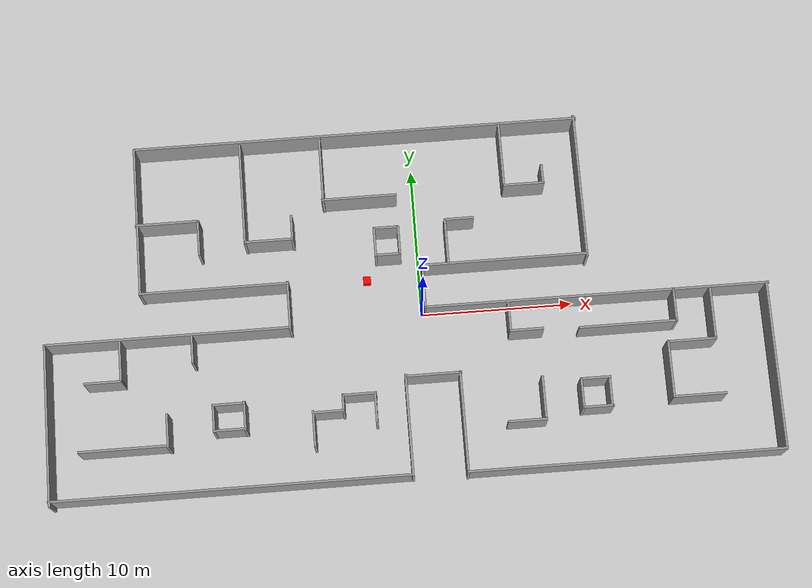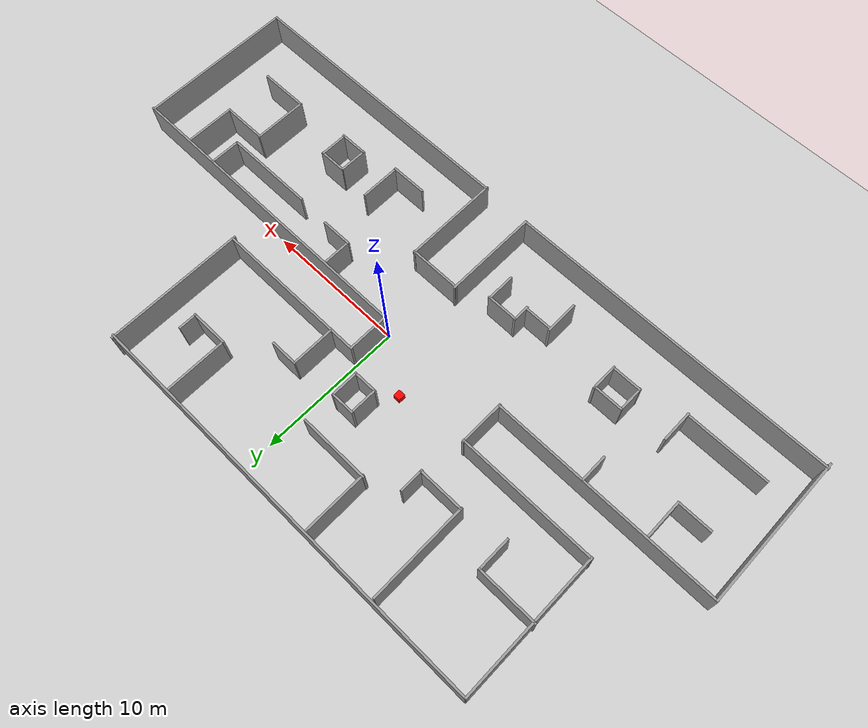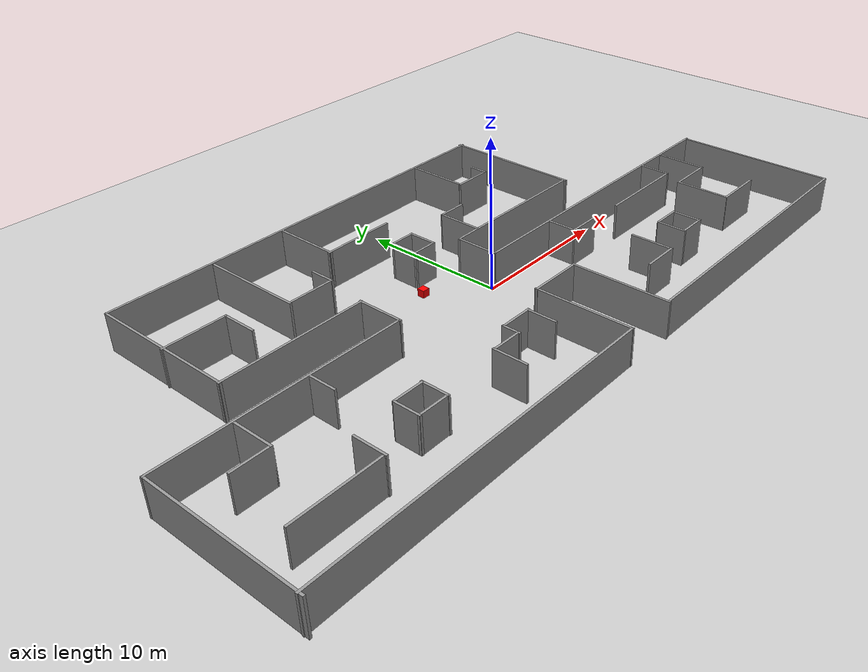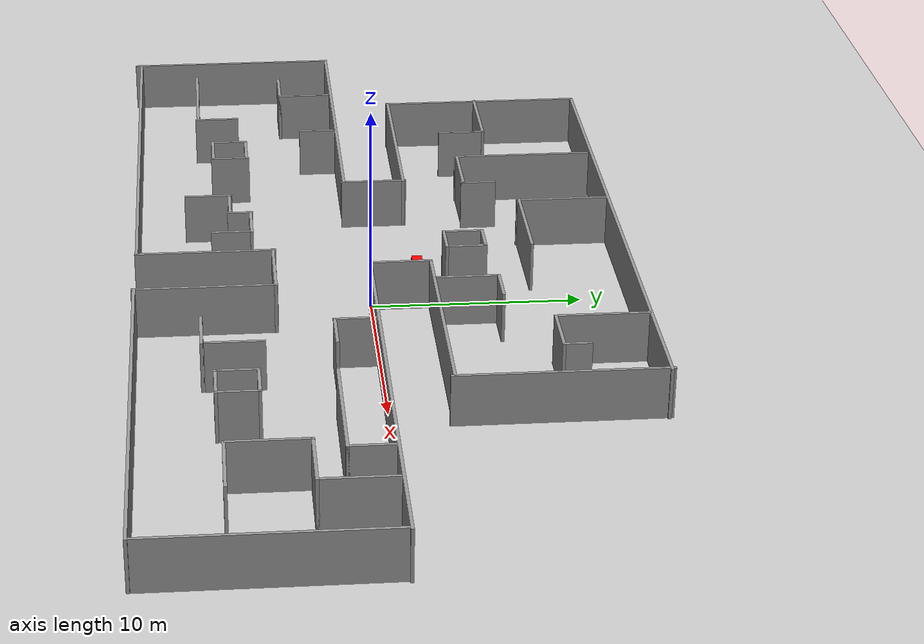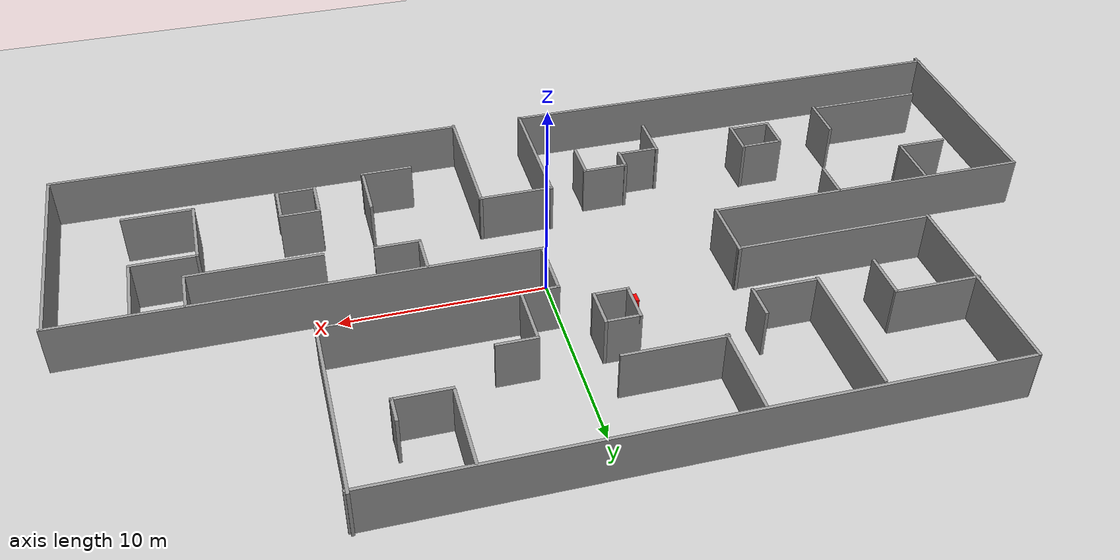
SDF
<sdf version="1.7">
 <world name="default">
  <light name="sun" type="directional">
   <pose>0 0 10 0 -0 0</pose>
   <diffuse>0.8 0.8 0.8 1</diffuse>
   <specular>0.2 0.2 0.2 1</specular>
   <attenuation>
    <range>1000</range>
    <constant>0.9</constant>
    <linear>0.01</linear>
    <quadratic>0.001</quadratic>
   </attenuation>
   <direction>-0.5 0.1 -0.9</direction>
   <spot><inner_angle>0</inner_angle><outer_angle>0</outer_angle><falloff>0</falloff></spot>
  </light>
  <model name="ground_plane">
   <static>1</static>
   <link name="link">
    <collision name="collision">
     <geometry><plane><normal>0 0 1</normal><size>100 100</size></plane></geometry>
     <surface>
      <contact><collide_bitmask>65535</collide_bitmask></contact>
      <friction><ode><mu>100</mu><mu2>50</mu2></ode></friction>
     </surface>
    </collision>
    <visual name="visual">
     <cast_shadows>0</cast_shadows>
     <geometry><plane><normal>0 0 1</normal><size>100 100</size></plane></geometry>
     <material>
      <script><uri>file://media/materials/scripts/gazebo.material</uri><name>Gazebo/Grey</name></script>
     </material>
    </visual>
   </link>
  </model>
  <gravity>0 0 -9.8</gravity>
  <magnetic_field>6e-06 2.3e-05 -4.2e-05</magnetic_field>
  <atmosphere type="adiabatic"/>
  <physics type="ode">
   <max_step_size>0.001</max_step_size>
   <real_time_factor>1</real_time_factor>
   <real_time_update_rate>1000</real_time_update_rate>
  </physics>
  <scene><ambient>0.4 0.4 0.4 1</ambient><background>0.7 0.7 0.7 1</background><shadows>1</shadows></scene>
  <spherical_coordinates>
   <surface_model>EARTH_WGS84</surface_model>
   <latitude_deg>0</latitude_deg>
   <longitude_deg>0</longitude_deg>
   <elevation>0</elevation>
   <heading_deg>0</heading_deg>
  </spherical_coordinates>
  <model name="target_box">
   <pose>-3.5 2.5 0.5 0 0 0</pose>
   <link name="link">
    <collision name="collision"><geometry><box><size>0.5 0.5 0.5</size></box></geometry></collision>
    <visual name="visual">
     <geometry><box><size>0.5 0.5 0.5</size></box></geometry>
     <material><ambient>1 0 0 1</ambient><diffuse>1 0 0 1</diffuse><specular>0.5 0.5 0.5 1</specular></material>
    </visual>
   </link>
  </model>
  <model name="newwoorld">
   <link name="Wall_101">
    <pose>-0.994043 4.5629 0 0 -0 3.14159</pose>
    <visual name="Wall_101_Visual">
     <pose>0 0 1.25 0 -0 0</pose>
     <geometry><box><size>1.75 0.15 2.5</size></box></geometry>
     <material>
      <script><uri>file://media/materials/scripts/gazebo.material</uri><name>Gazebo/Grey</name></script>
      <ambient>1 1 1 1</ambient>
      <shader type="pixel"/>
     </material>
     <meta><layer>0</layer></meta>
    </visual>
    <collision name="Wall_101_Collision">
     <pose>0 0 1.25 0 -0 0</pose>
     <geometry><box><size>1.75 0.15 2.5</size></box></geometry>
     <surface>
      <friction>
       <ode><mu>1</mu><mu2>1</mu2><fdir1>0 0 0</fdir1><slip1>0</slip1><slip2>0</slip2></ode>
       <torsional>
        <coefficient>1</coefficient>
        <patch_radius>0</patch_radius>
        <surface_radius>0</surface_radius>
        <use_patch_radius>1</use_patch_radius>
        <ode><slip>0</slip></ode>
       </torsional>
      </friction>
      <bounce><restitution_coefficient>0</restitution_coefficient><threshold>1e+06</threshold></bounce>
      <contact>
       <collide_without_contact>0</collide_without_contact>
       <collide_without_contact_bitmask>1</collide_without_contact_bitmask>
       <collide_bitmask>1</collide_bitmask>
       <ode>
        <soft_cfm>0</soft_cfm>
        <soft_erp>0.2</soft_erp>
        <kp>1e+13</kp>
        <kd>1</kd>
        <max_vel>0.01</max_vel>
        <min_depth>0</min_depth>
       </ode>
       <bullet>
        <split_impulse>1</split_impulse>
        <split_impulse_penetration_threshold>-0.01</split_impulse_penetration_threshold>
        <soft_cfm>0</soft_cfm>
        <soft_erp>0.2</soft_erp>
        <kp>1e+13</kp>
        <kd>1</kd>
       </bullet>
      </contact>
     </surface>
    </collision>
   </link>
   <link name="Wall_104">
    <pose>-0.194043 3.6379 0 0 0 -1.5708</pose>
    <visual name="Wall_104_Visual">
     <pose>0 0 1.25 0 -0 0</pose>
     <geometry><box><size>2 0.15 2.5</size></box></geometry>
     <material>
      <script><uri>file://media/materials/scripts/gazebo.material</uri><name>Gazebo/Grey</name></script>
      <ambient>1 1 1 1</ambient>
      <shader type="pixel"/>
     </material>
     <meta><layer>0</layer></meta>
    </visual>
    <collision name="Wall_104_Collision">
     <pose>0 0 1.25 0 -0 0</pose>
     <geometry><box><size>2 0.15 2.5</size></box></geometry>
     <surface>
      <friction>
       <ode><mu>1</mu><mu2>1</mu2><fdir1>0 0 0</fdir1><slip1>0</slip1><slip2>0</slip2></ode>
       <torsional>
        <coefficient>1</coefficient>
        <patch_radius>0</patch_radius>
        <surface_radius>0</surface_radius>
        <use_patch_radius>1</use_patch_radius>
        <ode><slip>0</slip></ode>
       </torsional>
      </friction>
      <bounce><restitution_coefficient>0</restitution_coefficient><threshold>1e+06</threshold></bounce>
      <contact>
       <collide_without_contact>0</collide_without_contact>
       <collide_without_contact_bitmask>1</collide_without_contact_bitmask>
       <collide_bitmask>1</collide_bitmask>
       <ode>
        <soft_cfm>0</soft_cfm>
        <soft_erp>0.2</soft_erp>
        <kp>1e+13</kp>
        <kd>1</kd>
        <max_vel>0.01</max_vel>
        <min_depth>0</min_depth>
       </ode>
       <bullet>
        <split_impulse>1</split_impulse>
        <split_impulse_penetration_threshold>-0.01</split_impulse_penetration_threshold>
        <soft_cfm>0</soft_cfm>
        <soft_erp>0.2</soft_erp>
        <kp>1e+13</kp>
        <kd>1</kd>
       </bullet>
      </contact>
     </surface>
    </collision>
   </link>
   <link name="Wall_105">
    <pose>-0.994043 2.7129 0 0 -0 3.14159</pose>
    <visual name="Wall_105_Visual">
     <pose>0 0 1.25 0 -0 0</pose>
     <geometry><box><size>1.75 0.15 2.5</size></box></geometry>
     <material>
      <script><uri>file://media/materials/scripts/gazebo.material</uri><name>Gazebo/Grey</name></script>
      <ambient>1 1 1 1</ambient>
      <shader type="pixel"/>
     </material>
     <meta><layer>0</layer></meta>
    </visual>
    <collision name="Wall_105_Collision">
     <pose>0 0 1.25 0 -0 0</pose>
     <geometry><box><size>1.75 0.15 2.5</size></box></geometry>
     <surface>
      <friction>
       <ode><mu>1</mu><mu2>1</mu2><fdir1>0 0 0</fdir1><slip1>0</slip1><slip2>0</slip2></ode>
       <torsional>
        <coefficient>1</coefficient>
        <patch_radius>0</patch_radius>
        <surface_radius>0</surface_radius>
        <use_patch_radius>1</use_patch_radius>
        <ode><slip>0</slip></ode>
       </torsional>
      </friction>
      <bounce><restitution_coefficient>0</restitution_coefficient><threshold>1e+06</threshold></bounce>
      <contact>
       <collide_without_contact>0</collide_without_contact>
       <collide_without_contact_bitmask>1</collide_without_contact_bitmask>
       <collide_bitmask>1</collide_bitmask>
       <ode>
        <soft_cfm>0</soft_cfm>
        <soft_erp>0.2</soft_erp>
        <kp>1e+13</kp>
        <kd>1</kd>
        <max_vel>0.01</max_vel>
        <min_depth>0</min_depth>
       </ode>
       <bullet>
        <split_impulse>1</split_impulse>
        <split_impulse_penetration_threshold>-0.01</split_impulse_penetration_threshold>
        <soft_cfm>0</soft_cfm>
        <soft_erp>0.2</soft_erp>
        <kp>1e+13</kp>
        <kd>1</kd>
       </bullet>
      </contact>
     </surface>
    </collision>
   </link>
   <link name="Wall_106">
    <pose>-1.79404 3.6379 0 0 -0 1.5708</pose>
    <visual name="Wall_106_Visual">
     <pose>0 0 1.25 0 -0 0</pose>
     <geometry><box><size>2 0.15 2.5</size></box></geometry>
     <material>
      <script><uri>file://media/materials/scripts/gazebo.material</uri><name>Gazebo/Grey</name></script>
      <ambient>1 1 1 1</ambient>
      <shader type="pixel"/>
     </material>
     <meta><layer>0</layer></meta>
    </visual>
    <collision name="Wall_106_Collision">
     <pose>0 0 1.25 0 -0 0</pose>
     <geometry><box><size>2 0.15 2.5</size></box></geometry>
     <surface>
      <friction>
       <ode><mu>1</mu><mu2>1</mu2><fdir1>0 0 0</fdir1><slip1>0</slip1><slip2>0</slip2></ode>
       <torsional>
        <coefficient>1</coefficient>
        <patch_radius>0</patch_radius>
        <surface_radius>0</surface_radius>
        <use_patch_radius>1</use_patch_radius>
        <ode><slip>0</slip></ode>
       </torsional>
      </friction>
      <bounce><restitution_coefficient>0</restitution_coefficient><threshold>1e+06</threshold></bounce>
      <contact>
       <collide_without_contact>0</collide_without_contact>
       <collide_without_contact_bitmask>1</collide_without_contact_bitmask>
       <collide_bitmask>1</collide_bitmask>
       <ode>
        <soft_cfm>0</soft_cfm>
        <soft_erp>0.2</soft_erp>
        <kp>1e+13</kp>
        <kd>1</kd>
        <max_vel>0.01</max_vel>
        <min_depth>0</min_depth>
       </ode>
       <bullet>
        <split_impulse>1</split_impulse>
        <split_impulse_penetration_threshold>-0.01</split_impulse_penetration_threshold>
        <soft_cfm>0</soft_cfm>
        <soft_erp>0.2</soft_erp>
        <kp>1e+13</kp>
        <kd>1</kd>
       </bullet>
      </contact>
     </surface>
    </collision>
   </link>
   <link name="Wall_109">
    <pose>14.3711 -3.20093 0 0 -0 3.14159</pose>
    <visual name="Wall_109_Visual">
     <pose>0 0 1.25 0 -0 0</pose>
     <geometry><box><size>6.5 0.15 2.5</size></box></geometry>
     <material>
      <script><uri>file://media/materials/scripts/gazebo.material</uri><name>Gazebo/Grey</name></script>
      <ambient>1 1 1 1</ambient>
      <shader type="pixel"/>
     </material>
     <meta><layer>0</layer></meta>
    </visual>
    <collision name="Wall_109_Collision">
     <pose>0 0 1.25 0 -0 0</pose>
     <geometry><box><size>6.5 0.15 2.5</size></box></geometry>
     <surface>
      <friction>
       <ode><mu>1</mu><mu2>1</mu2><fdir1>0 0 0</fdir1><slip1>0</slip1><slip2>0</slip2></ode>
       <torsional>
        <coefficient>1</coefficient>
        <patch_radius>0</patch_radius>
        <surface_radius>0</surface_radius>
        <use_patch_radius>1</use_patch_radius>
        <ode><slip>0</slip></ode>
       </torsional>
      </friction>
      <bounce><restitution_coefficient>0</restitution_coefficient><threshold>1e+06</threshold></bounce>
      <contact>
       <collide_without_contact>0</collide_without_contact>
       <collide_without_contact_bitmask>1</collide_without_contact_bitmask>
       <collide_bitmask>1</collide_bitmask>
       <ode>
        <soft_cfm>0</soft_cfm>
        <soft_erp>0.2</soft_erp>
        <kp>1e+13</kp>
        <kd>1</kd>
        <max_vel>0.01</max_vel>
        <min_depth>0</min_depth>
       </ode>
       <bullet>
        <split_impulse>1</split_impulse>
        <split_impulse_penetration_threshold>-0.01</split_impulse_penetration_threshold>
        <soft_cfm>0</soft_cfm>
        <soft_erp>0.2</soft_erp>
        <kp>1e+13</kp>
        <kd>1</kd>
       </bullet>
      </contact>
     </surface>
    </collision>
   </link>
   <link name="Wall_113">
    <pose>11.8737 -6.61393 0 0 -0 3.14159</pose>
    <visual name="Wall_113_Visual">
     <pose>0 0 1.25 0 -0 0</pose>
     <geometry><box><size>2 0.15 2.5</size></box></geometry>
     <material>
      <script><uri>file://media/materials/scripts/gazebo.material</uri><name>Gazebo/Grey</name></script>
      <ambient>1 1 1 1</ambient>
      <shader type="pixel"/>
     </material>
     <meta><layer>0</layer></meta>
    </visual>
    <collision name="Wall_113_Collision">
     <pose>0 0 1.25 0 -0 0</pose>
     <geometry><box><size>2 0.15 2.5</size></box></geometry>
     <surface>
      <friction>
       <ode><mu>1</mu><mu2>1</mu2><fdir1>0 0 0</fdir1><slip1>0</slip1><slip2>0</slip2></ode>
       <torsional>
        <coefficient>1</coefficient>
        <patch_radius>0</patch_radius>
        <surface_radius>0</surface_radius>
        <use_patch_radius>1</use_patch_radius>
        <ode><slip>0</slip></ode>
       </torsional>
      </friction>
      <bounce><restitution_coefficient>0</restitution_coefficient><threshold>1e+06</threshold></bounce>
      <contact>
       <collide_without_contact>0</collide_without_contact>
       <collide_without_contact_bitmask>1</collide_without_contact_bitmask>
       <collide_bitmask>1</collide_bitmask>
       <ode>
        <soft_cfm>0</soft_cfm>
        <soft_erp>0.2</soft_erp>
        <kp>1e+13</kp>
        <kd>1</kd>
        <max_vel>0.01</max_vel>
        <min_depth>0</min_depth>
       </ode>
       <bullet>
        <split_impulse>1</split_impulse>
        <split_impulse_penetration_threshold>-0.01</split_impulse_penetration_threshold>
        <soft_cfm>0</soft_cfm>
        <soft_erp>0.2</soft_erp>
        <kp>1e+13</kp>
        <kd>1</kd>
       </bullet>
      </contact>
     </surface>
    </collision>
   </link>
   <link name="Wall_114">
    <pose>10.928 -7.59269 0 0 0 -1.5708</pose>
    <visual name="Wall_114_Visual">
     <pose>0 0 1.25 0 -0 0</pose>
     <geometry><box><size>2 0.15 2.5</size></box></geometry>
     <material>
      <script><uri>file://media/materials/scripts/gazebo.material</uri><name>Gazebo/Grey</name></script>
      <ambient>1 1 1 1</ambient>
      <shader type="pixel"/>
     </material>
     <meta><layer>0</layer></meta>
    </visual>
    <collision name="Wall_114_Collision">
     <pose>0 0 1.25 0 -0 0</pose>
     <geometry><box><size>2 0.15 2.5</size></box></geometry>
     <surface>
      <friction>
       <ode><mu>1</mu><mu2>1</mu2><fdir1>0 0 0</fdir1><slip1>0</slip1><slip2>0</slip2></ode>
       <torsional>
        <coefficient>1</coefficient>
        <patch_radius>0</patch_radius>
        <surface_radius>0</surface_radius>
        <use_patch_radius>1</use_patch_radius>
        <ode><slip>0</slip></ode>
       </torsional>
      </friction>
      <bounce><restitution_coefficient>0</restitution_coefficient><threshold>1e+06</threshold></bounce>
      <contact>
       <collide_without_contact>0</collide_without_contact>
       <collide_without_contact_bitmask>1</collide_without_contact_bitmask>
       <collide_bitmask>1</collide_bitmask>
       <ode>
        <soft_cfm>0</soft_cfm>
        <soft_erp>0.2</soft_erp>
        <kp>1e+13</kp>
        <kd>1</kd>
        <max_vel>0.01</max_vel>
        <min_depth>0</min_depth>
       </ode>
       <bullet>
        <split_impulse>1</split_impulse>
        <split_impulse_penetration_threshold>-0.01</split_impulse_penetration_threshold>
        <soft_cfm>0</soft_cfm>
        <soft_erp>0.2</soft_erp>
        <kp>1e+13</kp>
        <kd>1</kd>
       </bullet>
      </contact>
     </surface>
    </collision>
   </link>
   <link name="Wall_117">
    <pose>12.7692 -7.56461 0 0 0 -1.5708</pose>
    <visual name="Wall_117_Visual">
     <pose>0 0 1.25 0 -0 0</pose>
     <geometry><box><size>2 0.15 2.5</size></box></geometry>
     <material>
      <script><uri>file://media/materials/scripts/gazebo.material</uri><name>Gazebo/Grey</name></script>
      <ambient>1 1 1 1</ambient>
      <shader type="pixel"/>
     </material>
     <meta><layer>0</layer></meta>
    </visual>
    <collision name="Wall_117_Collision">
     <pose>0 0 1.25 0 -0 0</pose>
     <geometry><box><size>2 0.15 2.5</size></box></geometry>
     <surface>
      <friction>
       <ode><mu>1</mu><mu2>1</mu2><fdir1>0 0 0</fdir1><slip1>0</slip1><slip2>0</slip2></ode>
       <torsional>
        <coefficient>1</coefficient>
        <patch_radius>0</patch_radius>
        <surface_radius>0</surface_radius>
        <use_patch_radius>1</use_patch_radius>
        <ode><slip>0</slip></ode>
       </torsional>
      </friction>
      <bounce><restitution_coefficient>0</restitution_coefficient><threshold>1e+06</threshold></bounce>
      <contact>
       <collide_without_contact>0</collide_without_contact>
       <collide_without_contact_bitmask>1</collide_without_contact_bitmask>
       <collide_bitmask>1</collide_bitmask>
       <ode>
        <soft_cfm>0</soft_cfm>
        <soft_erp>0.2</soft_erp>
        <kp>1e+13</kp>
        <kd>1</kd>
        <max_vel>0.01</max_vel>
        <min_depth>0</min_depth>
       </ode>
       <bullet>
        <split_impulse>1</split_impulse>
        <split_impulse_penetration_threshold>-0.01</split_impulse_penetration_threshold>
        <soft_cfm>0</soft_cfm>
        <soft_erp>0.2</soft_erp>
        <kp>1e+13</kp>
        <kd>1</kd>
       </bullet>
      </contact>
     </surface>
    </collision>
   </link>
   <link name="Wall_118">
    <pose>11.9001 -8.50409 0 0 -0 3.14159</pose>
    <visual name="Wall_118_Visual">
     <pose>0 0 1.25 0 -0 0</pose>
     <geometry><box><size>2 0.15 2.5</size></box></geometry>
     <material>
      <script><uri>file://media/materials/scripts/gazebo.material</uri><name>Gazebo/Grey</name></script>
      <ambient>1 1 1 1</ambient>
      <shader type="pixel"/>
     </material>
     <meta><layer>0</layer></meta>
    </visual>
    <collision name="Wall_118_Collision">
     <pose>0 0 1.25 0 -0 0</pose>
     <geometry><box><size>2 0.15 2.5</size></box></geometry>
     <surface>
      <friction>
       <ode><mu>1</mu><mu2>1</mu2><fdir1>0 0 0</fdir1><slip1>0</slip1><slip2>0</slip2></ode>
       <torsional>
        <coefficient>1</coefficient>
        <patch_radius>0</patch_radius>
        <surface_radius>0</surface_radius>
        <use_patch_radius>1</use_patch_radius>
        <ode><slip>0</slip></ode>
       </torsional>
      </friction>
      <bounce><restitution_coefficient>0</restitution_coefficient><threshold>1e+06</threshold></bounce>
      <contact>
       <collide_without_contact>0</collide_without_contact>
       <collide_without_contact_bitmask>1</collide_without_contact_bitmask>
       <collide_bitmask>1</collide_bitmask>
       <ode>
        <soft_cfm>0</soft_cfm>
        <soft_erp>0.2</soft_erp>
        <kp>1e+13</kp>
        <kd>1</kd>
        <max_vel>0.01</max_vel>
        <min_depth>0</min_depth>
       </ode>
       <bullet>
        <split_impulse>1</split_impulse>
        <split_impulse_penetration_threshold>-0.01</split_impulse_penetration_threshold>
        <soft_cfm>0</soft_cfm>
        <soft_erp>0.2</soft_erp>
        <kp>1e+13</kp>
        <kd>1</kd>
       </bullet>
      </contact>
     </surface>
    </collision>
   </link>
   <link name="Wall_120">
    <pose>7.23265 -9.0668 0 0 -0 0</pose>
    <inertial>
     <inertia><ixx>0</ixx><ixy>0</ixy><ixz>0</ixz><iyy>0</iyy><iyz>0</iyz><izz>0</izz></inertia>
     <mass>0</mass>
    </inertial>
    <visual name="Wall_120_Visual">
     <pose>0 0 1.25 0 -0 0</pose>
     <geometry><box><size>2.57319 0.15 2.5</size></box></geometry>
     <material>
      <script><uri>file://media/materials/scripts/gazebo.material</uri><name>Gazebo/Grey</name></script>
      <ambient>1 1 1 1</ambient>
      <shader type="pixel"/>
     </material>
     <meta><layer>0</layer></meta>
    </visual>
    <collision name="Wall_120_Collision">
     <pose>0 0 1.25 0 -0 0</pose>
     <geometry><box><size>2.57319 0.15 2.5</size></box></geometry>
     <surface>
      <friction>
       <ode><mu>1</mu><mu2>1</mu2><fdir1>0 0 0</fdir1><slip1>0</slip1><slip2>0</slip2></ode>
       <torsional>
        <coefficient>1</coefficient>
        <patch_radius>0</patch_radius>
        <surface_radius>0</surface_radius>
        <use_patch_radius>1</use_patch_radius>
        <ode><slip>0</slip></ode>
       </torsional>
      </friction>
      <bounce><restitution_coefficient>0</restitution_coefficient><threshold>1e+06</threshold></bounce>
      <contact>
       <collide_without_contact>0</collide_without_contact>
       <collide_without_contact_bitmask>1</collide_without_contact_bitmask>
       <collide_bitmask>1</collide_bitmask>
       <ode>
        <soft_cfm>0</soft_cfm>
        <soft_erp>0.2</soft_erp>
        <kp>1e+13</kp>
        <kd>1</kd>
        <max_vel>0.01</max_vel>
        <min_depth>0</min_depth>
       </ode>
       <bullet>
        <split_impulse>1</split_impulse>
        <split_impulse_penetration_threshold>-0.01</split_impulse_penetration_threshold>
        <soft_cfm>0</soft_cfm>
        <soft_erp>0.2</soft_erp>
        <kp>1e+13</kp>
        <kd>1</kd>
       </bullet>
      </contact>
     </surface>
    </collision>
   </link>
   <link name="Wall_124">
    <pose>6.64457 -2.03412 0 0 0 -1.5708</pose>
    <visual name="Wall_124_Visual">
     <pose>0 0 1.25 0 -0 0</pose>
     <geometry><box><size>2 0.15 2.5</size></box></geometry>
     <material>
      <script><uri>file://media/materials/scripts/gazebo.material</uri><name>Gazebo/Grey</name></script>
      <ambient>1 1 1 1</ambient>
      <shader type="pixel"/>
     </material>
     <meta><layer>0</layer></meta>
    </visual>
    <collision name="Wall_124_Collision">
     <pose>0 0 1.25 0 -0 0</pose>
     <geometry><box><size>2 0.15 2.5</size></box></geometry>
     <surface>
      <friction>
       <ode><mu>1</mu><mu2>1</mu2><fdir1>0 0 0</fdir1><slip1>0</slip1><slip2>0</slip2></ode>
       <torsional>
        <coefficient>1</coefficient>
        <patch_radius>0</patch_radius>
        <surface_radius>0</surface_radius>
        <use_patch_radius>1</use_patch_radius>
        <ode><slip>0</slip></ode>
       </torsional>
      </friction>
      <bounce><restitution_coefficient>0</restitution_coefficient><threshold>1e+06</threshold></bounce>
      <contact>
       <collide_without_contact>0</collide_without_contact>
       <collide_without_contact_bitmask>1</collide_without_contact_bitmask>
       <collide_bitmask>1</collide_bitmask>
       <ode>
        <soft_cfm>0</soft_cfm>
        <soft_erp>0.2</soft_erp>
        <kp>1e+13</kp>
        <kd>1</kd>
        <max_vel>0.01</max_vel>
        <min_depth>0</min_depth>
       </ode>
       <bullet>
        <split_impulse>1</split_impulse>
        <split_impulse_penetration_threshold>-0.01</split_impulse_penetration_threshold>
        <soft_cfm>0</soft_cfm>
        <soft_erp>0.2</soft_erp>
        <kp>1e+13</kp>
        <kd>1</kd>
       </bullet>
      </contact>
     </surface>
    </collision>
   </link>
   <link name="Wall_125">
    <pose>7.69661 -3.06382 0 0 -0 0</pose>
    <visual name="Wall_125_Visual">
     <pose>0 0 1.25 0 -0 0</pose>
     <geometry><box><size>2.25 0.15 2.5</size></box></geometry>
     <material>
      <script><uri>file://media/materials/scripts/gazebo.material</uri><name>Gazebo/Grey</name></script>
      <ambient>1 1 1 1</ambient>
      <shader type="pixel"/>
     </material>
     <meta><layer>0</layer></meta>
    </visual>
    <collision name="Wall_125_Collision">
     <pose>0 0 1.25 0 -0 0</pose>
     <geometry><box><size>2.25 0.15 2.5</size></box></geometry>
     <surface>
      <friction>
       <ode><mu>1</mu><mu2>1</mu2><fdir1>0 0 0</fdir1><slip1>0</slip1><slip2>0</slip2></ode>
       <torsional>
        <coefficient>1</coefficient>
        <patch_radius>0</patch_radius>
        <surface_radius>0</surface_radius>
        <use_patch_radius>1</use_patch_radius>
        <ode><slip>0</slip></ode>
       </torsional>
      </friction>
      <bounce><restitution_coefficient>0</restitution_coefficient><threshold>1e+06</threshold></bounce>
      <contact>
       <collide_without_contact>0</collide_without_contact>
       <collide_without_contact_bitmask>1</collide_without_contact_bitmask>
       <collide_bitmask>1</collide_bitmask>
       <ode>
        <soft_cfm>0</soft_cfm>
        <soft_erp>0.2</soft_erp>
        <kp>1e+13</kp>
        <kd>1</kd>
        <max_vel>0.01</max_vel>
        <min_depth>0</min_depth>
       </ode>
       <bullet>
        <split_impulse>1</split_impulse>
        <split_impulse_penetration_threshold>-0.01</split_impulse_penetration_threshold>
        <soft_cfm>0</soft_cfm>
        <soft_erp>0.2</soft_erp>
        <kp>1e+13</kp>
        <kd>1</kd>
       </bullet>
      </contact>
     </surface>
    </collision>
   </link>
   <link name="Wall_126">
    <pose>8.42456 -7.58944 0 0 0 -1.5708</pose>
    <visual name="Wall_126_Visual">
     <pose>0 0 1.25 0 -0 0</pose>
     <geometry><box><size>2.75 0.15 2.5</size></box></geometry>
     <material>
      <script><uri>file://media/materials/scripts/gazebo.material</uri><name>Gazebo/Grey</name></script>
      <ambient>1 1 1 1</ambient>
      <shader type="pixel"/>
     </material>
     <meta><layer>0</layer></meta>
    </visual>
    <collision name="Wall_126_Collision">
     <pose>0 0 1.25 0 -0 0</pose>
     <geometry><box><size>2.75 0.15 2.5</size></box></geometry>
     <surface>
      <friction>
       <ode><mu>1</mu><mu2>1</mu2><fdir1>0 0 0</fdir1><slip1>0</slip1><slip2>0</slip2></ode>
       <torsional>
        <coefficient>1</coefficient>
        <patch_radius>0</patch_radius>
        <surface_radius>0</surface_radius>
        <use_patch_radius>1</use_patch_radius>
        <ode><slip>0</slip></ode>
       </torsional>
      </friction>
      <bounce><restitution_coefficient>0</restitution_coefficient><threshold>1e+06</threshold></bounce>
      <contact>
       <collide_without_contact>0</collide_without_contact>
       <collide_without_contact_bitmask>1</collide_without_contact_bitmask>
       <collide_bitmask>1</collide_bitmask>
       <ode>
        <soft_cfm>0</soft_cfm>
        <soft_erp>0.2</soft_erp>
        <kp>1e+13</kp>
        <kd>1</kd>
        <max_vel>0.01</max_vel>
        <min_depth>0</min_depth>
       </ode>
       <bullet>
        <split_impulse>1</split_impulse>
        <split_impulse_penetration_threshold>-0.01</split_impulse_penetration_threshold>
        <soft_cfm>0</soft_cfm>
        <soft_erp>0.2</soft_erp>
        <kp>1e+13</kp>
        <kd>1</kd>
       </bullet>
      </contact>
     </surface>
    </collision>
   </link>
   <link name="Wall_129">
    <pose>17.5461 -2.15094 0 0 -0 1.5708</pose>
    <visual name="Wall_129_Visual">
     <pose>0 0 1.25 0 -0 0</pose>
     <geometry><box><size>2.25 0.15 2.5</size></box></geometry>
     <material>
      <script><uri>file://media/materials/scripts/gazebo.material</uri><name>Gazebo/Grey</name></script>
      <ambient>1 1 1 1</ambient>
      <shader type="pixel"/>
     </material>
     <meta><layer>0</layer></meta>
    </visual>
    <collision name="Wall_129_Collision">
     <pose>0 0 1.25 0 -0 0</pose>
     <geometry><box><size>2.25 0.15 2.5</size></box></geometry>
     <surface>
      <friction>
       <ode><mu>1</mu><mu2>1</mu2><fdir1>0 0 0</fdir1><slip1>0</slip1><slip2>0</slip2></ode>
       <torsional>
        <coefficient>1</coefficient>
        <patch_radius>0</patch_radius>
        <surface_radius>0</surface_radius>
        <use_patch_radius>1</use_patch_radius>
        <ode><slip>0</slip></ode>
       </torsional>
      </friction>
      <bounce><restitution_coefficient>0</restitution_coefficient><threshold>1e+06</threshold></bounce>
      <contact>
       <collide_without_contact>0</collide_without_contact>
       <collide_without_contact_bitmask>1</collide_without_contact_bitmask>
       <collide_bitmask>1</collide_bitmask>
       <ode>
        <soft_cfm>0</soft_cfm>
        <soft_erp>0.2</soft_erp>
        <kp>1e+13</kp>
        <kd>1</kd>
        <max_vel>0.01</max_vel>
        <min_depth>0</min_depth>
       </ode>
       <bullet>
        <split_impulse>1</split_impulse>
        <split_impulse_penetration_threshold>-0.01</split_impulse_penetration_threshold>
        <soft_cfm>0</soft_cfm>
        <soft_erp>0.2</soft_erp>
        <kp>1e+13</kp>
        <kd>1</kd>
       </bullet>
      </contact>
     </surface>
    </collision>
   </link>
   <link name="Wall_131">
    <pose>19.9598 -2.90481 0 0 0 -1.5708</pose>
    <visual name="Wall_131_Visual">
     <pose>0 0 1.25 0 -0 0</pose>
     <geometry><box><size>3.5 0.15 2.5</size></box></geometry>
     <material>
      <script><uri>file://media/materials/scripts/gazebo.material</uri><name>Gazebo/Grey</name></script>
      <ambient>1 1 1 1</ambient>
      <shader type="pixel"/>
     </material>
     <meta><layer>0</layer></meta>
    </visual>
    <collision name="Wall_131_Collision">
     <pose>0 0 1.25 0 -0 0</pose>
     <geometry><box><size>3.5 0.15 2.5</size></box></geometry>
     <surface>
      <friction>
       <ode><mu>1</mu><mu2>1</mu2><fdir1>0 0 0</fdir1><slip1>0</slip1><slip2>0</slip2></ode>
       <torsional>
        <coefficient>1</coefficient>
        <patch_radius>0</patch_radius>
        <surface_radius>0</surface_radius>
        <use_patch_radius>1</use_patch_radius>
        <ode><slip>0</slip></ode>
       </torsional>
      </friction>
      <bounce><restitution_coefficient>0</restitution_coefficient><threshold>1e+06</threshold></bounce>
      <contact>
       <collide_without_contact>0</collide_without_contact>
       <collide_without_contact_bitmask>1</collide_without_contact_bitmask>
       <collide_bitmask>1</collide_bitmask>
       <ode>
        <soft_cfm>0</soft_cfm>
        <soft_erp>0.2</soft_erp>
        <kp>1e+13</kp>
        <kd>1</kd>
        <max_vel>0.01</max_vel>
        <min_depth>0</min_depth>
       </ode>
       <bullet>
        <split_impulse>1</split_impulse>
        <split_impulse_penetration_threshold>-0.01</split_impulse_penetration_threshold>
        <soft_cfm>0</soft_cfm>
        <soft_erp>0.2</soft_erp>
        <kp>1e+13</kp>
        <kd>1</kd>
       </bullet>
      </contact>
     </surface>
    </collision>
   </link>
   <link name="Wall_132">
    <pose>18.4098 -4.57981 0 0 -0 3.14159</pose>
    <visual name="Wall_132_Visual">
     <pose>0 0 1.25 0 -0 0</pose>
     <geometry><box><size>3.25 0.15 2.5</size></box></geometry>
     <material>
      <script><uri>file://media/materials/scripts/gazebo.material</uri><name>Gazebo/Grey</name></script>
      <ambient>1 1 1 1</ambient>
      <shader type="pixel"/>
     </material>
     <meta><layer>0</layer></meta>
    </visual>
    <collision name="Wall_132_Collision">
     <pose>0 0 1.25 0 -0 0</pose>
     <geometry><box><size>3.25 0.15 2.5</size></box></geometry>
     <surface>
      <friction>
       <ode><mu>1</mu><mu2>1</mu2><fdir1>0 0 0</fdir1><slip1>0</slip1><slip2>0</slip2></ode>
       <torsional>
        <coefficient>1</coefficient>
        <patch_radius>0</patch_radius>
        <surface_radius>0</surface_radius>
        <use_patch_radius>1</use_patch_radius>
        <ode><slip>0</slip></ode>
       </torsional>
      </friction>
      <bounce><restitution_coefficient>0</restitution_coefficient><threshold>1e+06</threshold></bounce>
      <contact>
       <collide_without_contact>0</collide_without_contact>
       <collide_without_contact_bitmask>1</collide_without_contact_bitmask>
       <collide_bitmask>1</collide_bitmask>
       <ode>
        <soft_cfm>0</soft_cfm>
        <soft_erp>0.2</soft_erp>
        <kp>1e+13</kp>
        <kd>1</kd>
        <max_vel>0.01</max_vel>
        <min_depth>0</min_depth>
       </ode>
       <bullet>
        <split_impulse>1</split_impulse>
        <split_impulse_penetration_threshold>-0.01</split_impulse_penetration_threshold>
        <soft_cfm>0</soft_cfm>
        <soft_erp>0.2</soft_erp>
        <kp>1e+13</kp>
        <kd>1</kd>
       </bullet>
      </contact>
     </surface>
    </collision>
   </link>
   <link name="Wall_133">
    <pose>16.8377 -6.39924 0 0 0 -1.5708</pose>
    <inertial>
     <inertia><ixx>0</ixx><ixy>0</ixy><ixz>0</ixz><iyy>0</iyy><iyz>0</iyz><izz>0</izz></inertia>
     <mass>0</mass>
    </inertial>
    <visual name="Wall_133_Visual">
     <pose>0 0 1.25 0 -0 0</pose>
     <geometry><box><size>3.80144 0.15 2.5</size></box></geometry>
     <material>
      <script><uri>file://media/materials/scripts/gazebo.material</uri><name>Gazebo/Grey</name></script>
      <ambient>1 1 1 1</ambient>
      <shader type="pixel"/>
     </material>
     <meta><layer>0</layer></meta>
    </visual>
    <collision name="Wall_133_Collision">
     <pose>0 0 1.25 0 -0 0</pose>
     <geometry><box><size>3.80144 0.15 2.5</size></box></geometry>
     <surface>
      <friction>
       <ode><mu>1</mu><mu2>1</mu2><fdir1>0 0 0</fdir1><slip1>0</slip1><slip2>0</slip2></ode>
       <torsional>
        <coefficient>1</coefficient>
        <patch_radius>0</patch_radius>
        <surface_radius>0</surface_radius>
        <use_patch_radius>1</use_patch_radius>
        <ode><slip>0</slip></ode>
       </torsional>
      </friction>
      <bounce><restitution_coefficient>0</restitution_coefficient><threshold>1e+06</threshold></bounce>
      <contact>
       <collide_without_contact>0</collide_without_contact>
       <collide_without_contact_bitmask>1</collide_without_contact_bitmask>
       <collide_bitmask>1</collide_bitmask>
       <ode>
        <soft_cfm>0</soft_cfm>
        <soft_erp>0.2</soft_erp>
        <kp>1e+13</kp>
        <kd>1</kd>
        <max_vel>0.01</max_vel>
        <min_depth>0</min_depth>
       </ode>
       <bullet>
        <split_impulse>1</split_impulse>
        <split_impulse_penetration_threshold>-0.01</split_impulse_penetration_threshold>
        <soft_cfm>0</soft_cfm>
        <soft_erp>0.2</soft_erp>
        <kp>1e+13</kp>
        <kd>1</kd>
       </bullet>
      </contact>
     </surface>
    </collision>
   </link>
   <link name="Wall_134">
    <pose>18.5366 -8.24941 0 0 -0 0</pose>
    <inertial>
     <inertia><ixx>0</ixx><ixy>0</ixy><ixz>0</ixz><iyy>0</iyy><iyz>0</iyz><izz>0</izz></inertia>
     <mass>0</mass>
    </inertial>
    <visual name="Wall_134_Visual">
     <pose>0 0 1.25 0 -0 0</pose>
     <geometry><box><size>3.50876 0.15 2.5</size></box></geometry>
     <material>
      <script><uri>file://media/materials/scripts/gazebo.material</uri><name>Gazebo/Grey</name></script>
      <ambient>1 1 1 1</ambient>
      <shader type="pixel"/>
     </material>
     <meta><layer>0</layer></meta>
    </visual>
    <collision name="Wall_134_Collision">
     <pose>0 0 1.25 0 -0 0</pose>
     <geometry><box><size>3.50876 0.15 2.5</size></box></geometry>
     <surface>
      <friction>
       <ode><mu>1</mu><mu2>1</mu2><fdir1>0 0 0</fdir1><slip1>0</slip1><slip2>0</slip2></ode>
       <torsional>
        <coefficient>1</coefficient>
        <patch_radius>0</patch_radius>
        <surface_radius>0</surface_radius>
        <use_patch_radius>1</use_patch_radius>
        <ode><slip>0</slip></ode>
       </torsional>
      </friction>
      <bounce><restitution_coefficient>0</restitution_coefficient><threshold>1e+06</threshold></bounce>
      <contact>
       <collide_without_contact>0</collide_without_contact>
       <collide_without_contact_bitmask>1</collide_without_contact_bitmask>
       <collide_bitmask>1</collide_bitmask>
       <ode>
        <soft_cfm>0</soft_cfm>
        <soft_erp>0.2</soft_erp>
        <kp>1e+13</kp>
        <kd>1</kd>
        <max_vel>0.01</max_vel>
        <min_depth>0</min_depth>
       </ode>
       <bullet>
        <split_impulse>1</split_impulse>
        <split_impulse_penetration_threshold>-0.01</split_impulse_penetration_threshold>
        <soft_cfm>0</soft_cfm>
        <soft_erp>0.2</soft_erp>
        <kp>1e+13</kp>
        <kd>1</kd>
       </bullet>
      </contact>
     </surface>
    </collision>
   </link>
   <link name="Wall_137">
    <pose>-4.6097 -7.02476 0 0 -0 1.5708</pose>
    <visual name="Wall_137_Visual">
     <pose>0 0 1.25 0 -0 0</pose>
     <geometry><box><size>1.25 0.15 2.5</size></box></geometry>
     <material>
      <script><uri>file://media/materials/scripts/gazebo.material</uri><name>Gazebo/Grey</name></script>
      <ambient>1 1 1 1</ambient>
      <shader type="pixel"/>
     </material>
     <meta><layer>0</layer></meta>
    </visual>
    <collision name="Wall_137_Collision">
     <pose>0 0 1.25 0 -0 0</pose>
     <geometry><box><size>1.25 0.15 2.5</size></box></geometry>
     <surface>
      <friction>
       <ode><mu>1</mu><mu2>1</mu2><fdir1>0 0 0</fdir1><slip1>0</slip1><slip2>0</slip2></ode>
       <torsional>
        <coefficient>1</coefficient>
        <patch_radius>0</patch_radius>
        <surface_radius>0</surface_radius>
        <use_patch_radius>1</use_patch_radius>
        <ode><slip>0</slip></ode>
       </torsional>
      </friction>
      <bounce><restitution_coefficient>0</restitution_coefficient><threshold>1e+06</threshold></bounce>
      <contact>
       <collide_without_contact>0</collide_without_contact>
       <collide_without_contact_bitmask>1</collide_without_contact_bitmask>
       <collide_bitmask>1</collide_bitmask>
       <ode>
        <soft_cfm>0</soft_cfm>
        <soft_erp>0.2</soft_erp>
        <kp>1e+13</kp>
        <kd>1</kd>
        <max_vel>0.01</max_vel>
        <min_depth>0</min_depth>
       </ode>
       <bullet>
        <split_impulse>1</split_impulse>
        <split_impulse_penetration_threshold>-0.01</split_impulse_penetration_threshold>
        <soft_cfm>0</soft_cfm>
        <soft_erp>0.2</soft_erp>
        <kp>1e+13</kp>
        <kd>1</kd>
       </bullet>
      </contact>
     </surface>
    </collision>
   </link>
   <link name="Wall_138">
    <pose>-3.52263 -6.50901 0 0 -0 0</pose>
    <visual name="Wall_138_Visual">
     <pose>0 0 1.25 0 -0 0</pose>
     <geometry><box><size>2.25 0.15 2.5</size></box></geometry>
     <material>
      <script><uri>file://media/materials/scripts/gazebo.material</uri><name>Gazebo/Grey</name></script>
      <ambient>1 1 1 1</ambient>
      <shader type="pixel"/>
     </material>
     <meta><layer>0</layer></meta>
    </visual>
    <collision name="Wall_138_Collision">
     <pose>0 0 1.25 0 -0 0</pose>
     <geometry><box><size>2.25 0.15 2.5</size></box></geometry>
     <surface>
      <friction>
       <ode><mu>1</mu><mu2>1</mu2><fdir1>0 0 0</fdir1><slip1>0</slip1><slip2>0</slip2></ode>
       <torsional>
        <coefficient>1</coefficient>
        <patch_radius>0</patch_radius>
        <surface_radius>0</surface_radius>
        <use_patch_radius>1</use_patch_radius>
        <ode><slip>0</slip></ode>
       </torsional>
      </friction>
      <bounce><restitution_coefficient>0</restitution_coefficient><threshold>1e+06</threshold></bounce>
      <contact>
       <collide_without_contact>0</collide_without_contact>
       <collide_without_contact_bitmask>1</collide_without_contact_bitmask>
       <collide_bitmask>1</collide_bitmask>
       <ode>
        <soft_cfm>0</soft_cfm>
        <soft_erp>0.2</soft_erp>
        <kp>1e+13</kp>
        <kd>1</kd>
        <max_vel>0.01</max_vel>
        <min_depth>0</min_depth>
       </ode>
       <bullet>
        <split_impulse>1</split_impulse>
        <split_impulse_penetration_threshold>-0.01</split_impulse_penetration_threshold>
        <soft_cfm>0</soft_cfm>
        <soft_erp>0.2</soft_erp>
        <kp>1e+13</kp>
        <kd>1</kd>
       </bullet>
      </contact>
     </surface>
    </collision>
   </link>
   <link name="Wall_139">
    <pose>-2.51043 -7.50139 0 0 0 -1.5708</pose>
    <inertial>
     <inertia><ixx>0</ixx><ixy>0</ixy><ixz>0</ixz><iyy>0</iyy><iyz>0</iyz><izz>0</izz></inertia>
     <mass>0</mass>
    </inertial>
    <visual name="Wall_139_Visual">
     <pose>0 0 1.25 0 -0 0</pose>
     <geometry><box><size>1.94256 0.15 2.5</size></box></geometry>
     <material>
      <script><uri>file://media/materials/scripts/gazebo.material</uri><name>Gazebo/Grey</name></script>
      <ambient>1 1 1 1</ambient>
      <shader type="pixel"/>
     </material>
     <meta><layer>0</layer></meta>
    </visual>
    <collision name="Wall_139_Collision">
     <pose>0 0 1.25 0 -0 0</pose>
     <geometry><box><size>1.94256 0.15 2.5</size></box></geometry>
     <surface>
      <friction>
       <ode><mu>1</mu><mu2>1</mu2><fdir1>0 0 0</fdir1><slip1>0</slip1><slip2>0</slip2></ode>
       <torsional>
        <coefficient>1</coefficient>
        <patch_radius>0</patch_radius>
        <surface_radius>0</surface_radius>
        <use_patch_radius>1</use_patch_radius>
        <ode><slip>0</slip></ode>
       </torsional>
      </friction>
      <bounce><restitution_coefficient>0</restitution_coefficient><threshold>1e+06</threshold></bounce>
      <contact>
       <collide_without_contact>0</collide_without_contact>
       <collide_without_contact_bitmask>1</collide_without_contact_bitmask>
       <collide_bitmask>1</collide_bitmask>
       <ode>
        <soft_cfm>0</soft_cfm>
        <soft_erp>0.2</soft_erp>
        <kp>1e+13</kp>
        <kd>1</kd>
        <max_vel>0.01</max_vel>
        <min_depth>0</min_depth>
       </ode>
       <bullet>
        <split_impulse>1</split_impulse>
        <split_impulse_penetration_threshold>-0.01</split_impulse_penetration_threshold>
        <soft_cfm>0</soft_cfm>
        <soft_erp>0.2</soft_erp>
        <kp>1e+13</kp>
        <kd>1</kd>
       </bullet>
      </contact>
     </surface>
    </collision>
   </link>
   <link name="Wall_17">
    <pose>-2.56748 11.2292 0 0 -0 3.14159</pose>
    <visual name="Wall_17_Visual">
     <pose>0 0 1.25 0 -0 0</pose>
     <geometry><box><size>29.75 0.15 2.5</size></box></geometry>
     <material>
      <script><uri>file://media/materials/scripts/gazebo.material</uri><name>Gazebo/Grey</name></script>
      <ambient>1 1 1 1</ambient>
      <shader type="pixel"/>
     </material>
     <meta><layer>0</layer></meta>
    </visual>
    <collision name="Wall_17_Collision">
     <pose>0 0 1.25 0 -0 0</pose>
     <geometry><box><size>29.75 0.15 2.5</size></box></geometry>
     <surface>
      <friction>
       <ode><mu>1</mu><mu2>1</mu2><fdir1>0 0 0</fdir1><slip1>0</slip1><slip2>0</slip2></ode>
       <torsional>
        <coefficient>1</coefficient>
        <patch_radius>0</patch_radius>
        <surface_radius>0</surface_radius>
        <use_patch_radius>1</use_patch_radius>
        <ode><slip>0</slip></ode>
       </torsional>
      </friction>
      <bounce><restitution_coefficient>0</restitution_coefficient><threshold>1e+06</threshold></bounce>
      <contact>
       <collide_without_contact>0</collide_without_contact>
       <collide_without_contact_bitmask>1</collide_without_contact_bitmask>
       <collide_bitmask>1</collide_bitmask>
       <ode>
        <soft_cfm>0</soft_cfm>
        <soft_erp>0.2</soft_erp>
        <kp>1e+13</kp>
        <kd>1</kd>
        <max_vel>0.01</max_vel>
        <min_depth>0</min_depth>
       </ode>
       <bullet>
        <split_impulse>1</split_impulse>
        <split_impulse_penetration_threshold>-0.01</split_impulse_penetration_threshold>
        <soft_cfm>0</soft_cfm>
        <soft_erp>0.2</soft_erp>
        <kp>1e+13</kp>
        <kd>1</kd>
       </bullet>
      </contact>
     </surface>
    </collision>
   </link>
   <link name="Wall_19">
    <pose>-17.4304 6.21066 0 0 0 -1.5708</pose>
    <inertial>
     <inertia><ixx>0</ixx><ixy>0</ixy><ixz>0</ixz><iyy>0</iyy><iyz>0</iyz><izz>0</izz></inertia>
     <mass>0</mass>
    </inertial>
    <visual name="Wall_19_Visual">
     <pose>0 0 1.25 0 -0 0</pose>
     <geometry><box><size>10.1278 0.15 2.5</size></box></geometry>
     <material>
      <script><uri>file://media/materials/scripts/gazebo.material</uri><name>Gazebo/Grey</name></script>
      <ambient>1 1 1 1</ambient>
      <shader type="pixel"/>
     </material>
     <meta><layer>0</layer></meta>
    </visual>
    <collision name="Wall_19_Collision">
     <pose>0 0 1.25 0 -0 0</pose>
     <geometry><box><size>10.1278 0.15 2.5</size></box></geometry>
     <surface>
      <friction>
       <ode><mu>1</mu><mu2>1</mu2><fdir1>0 0 0</fdir1><slip1>0</slip1><slip2>0</slip2></ode>
       <torsional>
        <coefficient>1</coefficient>
        <patch_radius>0</patch_radius>
        <surface_radius>0</surface_radius>
        <use_patch_radius>1</use_patch_radius>
        <ode><slip>0</slip></ode>
       </torsional>
      </friction>
      <bounce><restitution_coefficient>0</restitution_coefficient><threshold>1e+06</threshold></bounce>
      <contact>
       <collide_without_contact>0</collide_without_contact>
       <collide_without_contact_bitmask>1</collide_without_contact_bitmask>
       <collide_bitmask>1</collide_bitmask>
       <ode>
        <soft_cfm>0</soft_cfm>
        <soft_erp>0.2</soft_erp>
        <kp>1e+13</kp>
        <kd>1</kd>
        <max_vel>0.01</max_vel>
        <min_depth>0</min_depth>
       </ode>
       <bullet>
        <split_impulse>1</split_impulse>
        <split_impulse_penetration_threshold>-0.01</split_impulse_penetration_threshold>
        <soft_cfm>0</soft_cfm>
        <soft_erp>0.2</soft_erp>
        <kp>1e+13</kp>
        <kd>1</kd>
       </bullet>
      </contact>
     </surface>
    </collision>
   </link>
   <link name="Wall_20">
    <pose>-12.5874 1.25548 0 0 -0 0</pose>
    <inertial>
     <inertia><ixx>0</ixx><ixy>0</ixy><ixz>0</ixz><iyy>0</iyy><iyz>0</iyz><izz>0</izz></inertia>
     <mass>0</mass>
    </inertial>
    <visual name="Wall_20_Visual">
     <pose>0 0 1.25 0 -0 0</pose>
     <geometry><box><size>9.89817 0.15 2.5</size></box></geometry>
     <material>
      <script><uri>file://media/materials/scripts/gazebo.material</uri><name>Gazebo/Grey</name></script>
      <ambient>1 1 1 1</ambient>
      <shader type="pixel"/>
     </material>
     <meta><layer>0</layer></meta>
    </visual>
    <collision name="Wall_20_Collision">
     <pose>0 0 1.25 0 -0 0</pose>
     <geometry><box><size>9.89817 0.15 2.5</size></box></geometry>
     <surface>
      <friction>
       <ode><mu>1</mu><mu2>1</mu2><fdir1>0 0 0</fdir1><slip1>0</slip1><slip2>0</slip2></ode>
       <torsional>
        <coefficient>1</coefficient>
        <patch_radius>0</patch_radius>
        <surface_radius>0</surface_radius>
        <use_patch_radius>1</use_patch_radius>
        <ode><slip>0</slip></ode>
       </torsional>
      </friction>
      <bounce><restitution_coefficient>0</restitution_coefficient><threshold>1e+06</threshold></bounce>
      <contact>
       <collide_without_contact>0</collide_without_contact>
       <collide_without_contact_bitmask>1</collide_without_contact_bitmask>
       <collide_bitmask>1</collide_bitmask>
       <ode>
        <soft_cfm>0</soft_cfm>
        <soft_erp>0.2</soft_erp>
        <kp>1e+13</kp>
        <kd>1</kd>
        <max_vel>0.01</max_vel>
        <min_depth>0</min_depth>
       </ode>
       <bullet>
        <split_impulse>1</split_impulse>
        <split_impulse_penetration_threshold>-0.01</split_impulse_penetration_threshold>
        <soft_cfm>0</soft_cfm>
        <soft_erp>0.2</soft_erp>
        <kp>1e+13</kp>
        <kd>1</kd>
       </bullet>
      </contact>
     </surface>
    </collision>
   </link>
   <link name="Wall_21">
    <pose>-7.73266 -0.233967 0 0 0 -1.5708</pose>
    <visual name="Wall_21_Visual">
     <pose>0 0 1.25 0 -0 0</pose>
     <geometry><box><size>3.25 0.15 2.5</size></box></geometry>
     <material>
      <script><uri>file://media/materials/scripts/gazebo.material</uri><name>Gazebo/Grey</name></script>
      <ambient>1 1 1 1</ambient>
      <shader type="pixel"/>
     </material>
     <meta><layer>0</layer></meta>
    </visual>
    <collision name="Wall_21_Collision">
     <pose>0 0 1.25 0 -0 0</pose>
     <geometry><box><size>3.25 0.15 2.5</size></box></geometry>
     <surface>
      <friction>
       <ode><mu>1</mu><mu2>1</mu2><fdir1>0 0 0</fdir1><slip1>0</slip1><slip2>0</slip2></ode>
       <torsional>
        <coefficient>1</coefficient>
        <patch_radius>0</patch_radius>
        <surface_radius>0</surface_radius>
        <use_patch_radius>1</use_patch_radius>
        <ode><slip>0</slip></ode>
       </torsional>
      </friction>
      <bounce><restitution_coefficient>0</restitution_coefficient><threshold>1e+06</threshold></bounce>
      <contact>
       <collide_without_contact>0</collide_without_contact>
       <collide_without_contact_bitmask>1</collide_without_contact_bitmask>
       <collide_bitmask>1</collide_bitmask>
       <ode>
        <soft_cfm>0</soft_cfm>
        <soft_erp>0.2</soft_erp>
        <kp>1e+13</kp>
        <kd>1</kd>
        <max_vel>0.01</max_vel>
        <min_depth>0</min_depth>
       </ode>
       <bullet>
        <split_impulse>1</split_impulse>
        <split_impulse_penetration_threshold>-0.01</split_impulse_penetration_threshold>
        <soft_cfm>0</soft_cfm>
        <soft_erp>0.2</soft_erp>
        <kp>1e+13</kp>
        <kd>1</kd>
       </bullet>
      </contact>
     </surface>
    </collision>
   </link>
   <link name="Wall_22">
    <pose>-15.8089 -1.73498 0 0 -0 3.14159</pose>
    <inertial>
     <inertia><ixx>0</ixx><ixy>0</ixy><ixz>0</ixz><iyy>0</iyy><iyz>0</iyz><izz>0</izz></inertia>
     <mass>0</mass>
    </inertial>
    <visual name="Wall_22_Visual">
     <pose>0 0 1.25 0 -0 0</pose>
     <geometry><box><size>16.191 0.15 2.5</size></box></geometry>
     <material>
      <script><uri>file://media/materials/scripts/gazebo.material</uri><name>Gazebo/Grey</name></script>
      <ambient>1 1 1 1</ambient>
      <shader type="pixel"/>
     </material>
     <meta><layer>0</layer></meta>
    </visual>
    <collision name="Wall_22_Collision">
     <pose>0 0 1.25 0 -0 0</pose>
     <geometry><box><size>16.191 0.15 2.5</size></box></geometry>
     <surface>
      <friction>
       <ode><mu>1</mu><mu2>1</mu2><fdir1>0 0 0</fdir1><slip1>0</slip1><slip2>0</slip2></ode>
       <torsional>
        <coefficient>1</coefficient>
        <patch_radius>0</patch_radius>
        <surface_radius>0</surface_radius>
        <use_patch_radius>1</use_patch_radius>
        <ode><slip>0</slip></ode>
       </torsional>
      </friction>
      <bounce><restitution_coefficient>0</restitution_coefficient><threshold>1e+06</threshold></bounce>
      <contact>
       <collide_without_contact>0</collide_without_contact>
       <collide_without_contact_bitmask>1</collide_without_contact_bitmask>
       <collide_bitmask>1</collide_bitmask>
       <ode>
        <soft_cfm>0</soft_cfm>
        <soft_erp>0.2</soft_erp>
        <kp>1e+13</kp>
        <kd>1</kd>
        <max_vel>0.01</max_vel>
        <min_depth>0</min_depth>
       </ode>
       <bullet>
        <split_impulse>1</split_impulse>
        <split_impulse_penetration_threshold>-0.01</split_impulse_penetration_threshold>
        <soft_cfm>0</soft_cfm>
        <soft_erp>0.2</soft_erp>
        <kp>1e+13</kp>
        <kd>1</kd>
       </bullet>
      </contact>
     </surface>
    </collision>
   </link>
   <link name="Wall_23">
    <pose>-23.8122 -7.0124 0 0 0 -1.5708</pose>
    <inertial>
     <inertia><ixx>0</ixx><ixy>0</ixy><ixz>0</ixz><iyy>0</iyy><iyz>0</iyz><izz>0</izz></inertia>
     <mass>0</mass>
    </inertial>
    <visual name="Wall_23_Visual">
     <pose>0 0 1.25 0 -0 0</pose>
     <geometry><box><size>10.6789 0.15 2.5</size></box></geometry>
     <material>
      <script><uri>file://media/materials/scripts/gazebo.material</uri><name>Gazebo/Grey</name></script>
      <ambient>1 1 1 1</ambient>
      <shader type="pixel"/>
     </material>
     <meta><layer>0</layer></meta>
    </visual>
    <collision name="Wall_23_Collision">
     <pose>0 0 1.25 0 -0 0</pose>
     <geometry><box><size>10.6789 0.15 2.5</size></box></geometry>
     <surface>
      <friction>
       <ode><mu>1</mu><mu2>1</mu2><fdir1>0 0 0</fdir1><slip1>0</slip1><slip2>0</slip2></ode>
       <torsional>
        <coefficient>1</coefficient>
        <patch_radius>0</patch_radius>
        <surface_radius>0</surface_radius>
        <use_patch_radius>1</use_patch_radius>
        <ode><slip>0</slip></ode>
       </torsional>
      </friction>
      <bounce><restitution_coefficient>0</restitution_coefficient><threshold>1e+06</threshold></bounce>
      <contact>
       <collide_without_contact>0</collide_without_contact>
       <collide_without_contact_bitmask>1</collide_without_contact_bitmask>
       <collide_bitmask>1</collide_bitmask>
       <ode>
        <soft_cfm>0</soft_cfm>
        <soft_erp>0.2</soft_erp>
        <kp>1e+13</kp>
        <kd>1</kd>
        <max_vel>0.01</max_vel>
        <min_depth>0</min_depth>
       </ode>
       <bullet>
        <split_impulse>1</split_impulse>
        <split_impulse_penetration_threshold>-0.01</split_impulse_penetration_threshold>
        <soft_cfm>0</soft_cfm>
        <soft_erp>0.2</soft_erp>
        <kp>1e+13</kp>
        <kd>1</kd>
       </bullet>
      </contact>
     </surface>
    </collision>
   </link>
   <link name="Wall_24">
    <pose>-12.1798 -12.0229 0 0 -0 0</pose>
    <visual name="Wall_24_Visual">
     <pose>0 0 1.25 0 -0 0</pose>
     <geometry><box><size>23.5 0.15 2.5</size></box></geometry>
     <material>
      <script><uri>file://media/materials/scripts/gazebo.material</uri><name>Gazebo/Grey</name></script>
      <ambient>1 1 1 1</ambient>
      <shader type="pixel"/>
     </material>
     <meta><layer>0</layer></meta>
    </visual>
    <collision name="Wall_24_Collision">
     <pose>0 0 1.25 0 -0 0</pose>
     <geometry><box><size>23.5 0.15 2.5</size></box></geometry>
     <surface>
      <friction>
       <ode><mu>1</mu><mu2>1</mu2><fdir1>0 0 0</fdir1><slip1>0</slip1><slip2>0</slip2></ode>
       <torsional>
        <coefficient>1</coefficient>
        <patch_radius>0</patch_radius>
        <surface_radius>0</surface_radius>
        <use_patch_radius>1</use_patch_radius>
        <ode><slip>0</slip></ode>
       </torsional>
      </friction>
      <bounce><restitution_coefficient>0</restitution_coefficient><threshold>1e+06</threshold></bounce>
      <contact>
       <collide_without_contact>0</collide_without_contact>
       <collide_without_contact_bitmask>1</collide_without_contact_bitmask>
       <collide_bitmask>1</collide_bitmask>
       <ode>
        <soft_cfm>0</soft_cfm>
        <soft_erp>0.2</soft_erp>
        <kp>1e+13</kp>
        <kd>1</kd>
        <max_vel>0.01</max_vel>
        <min_depth>0</min_depth>
       </ode>
       <bullet>
        <split_impulse>1</split_impulse>
        <split_impulse_penetration_threshold>-0.01</split_impulse_penetration_threshold>
        <soft_cfm>0</soft_cfm>
        <soft_erp>0.2</soft_erp>
        <kp>1e+13</kp>
        <kd>1</kd>
       </bullet>
      </contact>
     </surface>
    </collision>
   </link>
   <link name="Wall_25">
    <pose>-0.443123 -8.77584 0 0 -0 1.5708</pose>
    <inertial>
     <inertia><ixx>0</ixx><ixy>0</ixy><ixz>0</ixz><iyy>0</iyy><iyz>0</iyz><izz>0</izz></inertia>
     <mass>0</mass>
    </inertial>
    <visual name="Wall_25_Visual">
     <pose>0 0 1.25 0 -0 0</pose>
     <geometry><box><size>6.69625 0.15 2.5</size></box></geometry>
     <material>
      <script><uri>file://media/materials/scripts/gazebo.material</uri><name>Gazebo/Grey</name></script>
      <ambient>1 1 1 1</ambient>
      <shader type="pixel"/>
     </material>
     <meta><layer>0</layer></meta>
    </visual>
    <collision name="Wall_25_Collision">
     <pose>0 0 1.25 0 -0 0</pose>
     <geometry><box><size>6.69625 0.15 2.5</size></box></geometry>
     <surface>
      <friction>
       <ode><mu>1</mu><mu2>1</mu2><fdir1>0 0 0</fdir1><slip1>0</slip1><slip2>0</slip2></ode>
       <torsional>
        <coefficient>1</coefficient>
        <patch_radius>0</patch_radius>
        <surface_radius>0</surface_radius>
        <use_patch_radius>1</use_patch_radius>
        <ode><slip>0</slip></ode>
       </torsional>
      </friction>
      <bounce><restitution_coefficient>0</restitution_coefficient><threshold>1e+06</threshold></bounce>
      <contact>
       <collide_without_contact>0</collide_without_contact>
       <collide_without_contact_bitmask>1</collide_without_contact_bitmask>
       <collide_bitmask>1</collide_bitmask>
       <ode>
        <soft_cfm>0</soft_cfm>
        <soft_erp>0.2</soft_erp>
        <kp>1e+13</kp>
        <kd>1</kd>
        <max_vel>0.01</max_vel>
        <min_depth>0</min_depth>
       </ode>
       <bullet>
        <split_impulse>1</split_impulse>
        <split_impulse_penetration_threshold>-0.01</split_impulse_penetration_threshold>
        <soft_cfm>0</soft_cfm>
        <soft_erp>0.2</soft_erp>
        <kp>1e+13</kp>
        <kd>1</kd>
       </bullet>
      </contact>
     </surface>
    </collision>
   </link>
   <link name="Wall_26">
    <pose>1.3447 -5.57207 0 0 -0 0</pose>
    <visual name="Wall_26_Visual">
     <pose>0 0 1.25 0 -0 0</pose>
     <geometry><box><size>3.75 0.15 2.5</size></box></geometry>
     <material>
      <script><uri>file://media/materials/scripts/gazebo.material</uri><name>Gazebo/Grey</name></script>
      <ambient>1 1 1 1</ambient>
      <shader type="pixel"/>
     </material>
     <meta><layer>0</layer></meta>
    </visual>
    <collision name="Wall_26_Collision">
     <pose>0 0 1.25 0 -0 0</pose>
     <geometry><box><size>3.75 0.15 2.5</size></box></geometry>
     <surface>
      <friction>
       <ode><mu>1</mu><mu2>1</mu2><fdir1>0 0 0</fdir1><slip1>0</slip1><slip2>0</slip2></ode>
       <torsional>
        <coefficient>1</coefficient>
        <patch_radius>0</patch_radius>
        <surface_radius>0</surface_radius>
        <use_patch_radius>1</use_patch_radius>
        <ode><slip>0</slip></ode>
       </torsional>
      </friction>
      <bounce><restitution_coefficient>0</restitution_coefficient><threshold>1e+06</threshold></bounce>
      <contact>
       <collide_without_contact>0</collide_without_contact>
       <collide_without_contact_bitmask>1</collide_without_contact_bitmask>
       <collide_bitmask>1</collide_bitmask>
       <ode>
        <soft_cfm>0</soft_cfm>
        <soft_erp>0.2</soft_erp>
        <kp>1e+13</kp>
        <kd>1</kd>
        <max_vel>0.01</max_vel>
        <min_depth>0</min_depth>
       </ode>
       <bullet>
        <split_impulse>1</split_impulse>
        <split_impulse_penetration_threshold>-0.01</split_impulse_penetration_threshold>
        <soft_cfm>0</soft_cfm>
        <soft_erp>0.2</soft_erp>
        <kp>1e+13</kp>
        <kd>1</kd>
       </bullet>
      </contact>
     </surface>
    </collision>
   </link>
   <link name="Wall_27">
    <pose>3.11878 -8.86214 0 0 0 -1.5708</pose>
    <inertial>
     <inertia><ixx>0</ixx><ixy>0</ixy><ixz>0</ixz><iyy>0</iyy><iyz>0</iyz><izz>0</izz></inertia>
     <mass>0</mass>
    </inertial>
    <visual name="Wall_27_Visual">
     <pose>0 0 1.25 0 -0 0</pose>
     <geometry><box><size>6.77124 0.15 2.5</size></box></geometry>
     <material>
      <script><uri>file://media/materials/scripts/gazebo.material</uri><name>Gazebo/Grey</name></script>
      <ambient>1 1 1 1</ambient>
      <shader type="pixel"/>
     </material>
     <meta><layer>0</layer></meta>
    </visual>
    <collision name="Wall_27_Collision">
     <pose>0 0 1.25 0 -0 0</pose>
     <geometry><box><size>6.77124 0.15 2.5</size></box></geometry>
     <surface>
      <friction>
       <ode><mu>1</mu><mu2>1</mu2><fdir1>0 0 0</fdir1><slip1>0</slip1><slip2>0</slip2></ode>
       <torsional>
        <coefficient>1</coefficient>
        <patch_radius>0</patch_radius>
        <surface_radius>0</surface_radius>
        <use_patch_radius>1</use_patch_radius>
        <ode><slip>0</slip></ode>
       </torsional>
      </friction>
      <bounce><restitution_coefficient>0</restitution_coefficient><threshold>1e+06</threshold></bounce>
      <contact>
       <collide_without_contact>0</collide_without_contact>
       <collide_without_contact_bitmask>1</collide_without_contact_bitmask>
       <collide_bitmask>1</collide_bitmask>
       <ode>
        <soft_cfm>0</soft_cfm>
        <soft_erp>0.2</soft_erp>
        <kp>1e+13</kp>
        <kd>1</kd>
        <max_vel>0.01</max_vel>
        <min_depth>0</min_depth>
       </ode>
       <bullet>
        <split_impulse>1</split_impulse>
        <split_impulse_penetration_threshold>-0.01</split_impulse_penetration_threshold>
        <soft_cfm>0</soft_cfm>
        <soft_erp>0.2</soft_erp>
        <kp>1e+13</kp>
        <kd>1</kd>
       </bullet>
      </contact>
     </surface>
    </collision>
   </link>
   <link name="Wall_36">
    <pose>-18.9181 -3.19701 0 0 0 -1.5708</pose>
    <visual name="Wall_36_Visual">
     <pose>0 0 1.25 0 -0 0</pose>
     <geometry><box><size>2.75 0.15 2.5</size></box></geometry>
     <material>
      <script><uri>file://media/materials/scripts/gazebo.material</uri><name>Gazebo/Grey</name></script>
      <ambient>1 1 1 1</ambient>
      <shader type="pixel"/>
     </material>
     <meta><layer>0</layer></meta>
    </visual>
    <collision name="Wall_36_Collision">
     <pose>0 0 1.25 0 -0 0</pose>
     <geometry><box><size>2.75 0.15 2.5</size></box></geometry>
     <surface>
      <friction>
       <ode><mu>1</mu><mu2>1</mu2><fdir1>0 0 0</fdir1><slip1>0</slip1><slip2>0</slip2></ode>
       <torsional>
        <coefficient>1</coefficient>
        <patch_radius>0</patch_radius>
        <surface_radius>0</surface_radius>
        <use_patch_radius>1</use_patch_radius>
        <ode><slip>0</slip></ode>
       </torsional>
      </friction>
      <bounce><restitution_coefficient>0</restitution_coefficient><threshold>1e+06</threshold></bounce>
      <contact>
       <collide_without_contact>0</collide_without_contact>
       <collide_without_contact_bitmask>1</collide_without_contact_bitmask>
       <collide_bitmask>1</collide_bitmask>
       <ode>
        <soft_cfm>0</soft_cfm>
        <soft_erp>0.2</soft_erp>
        <kp>1e+13</kp>
        <kd>1</kd>
        <max_vel>0.01</max_vel>
        <min_depth>0</min_depth>
       </ode>
       <bullet>
        <split_impulse>1</split_impulse>
        <split_impulse_penetration_threshold>-0.01</split_impulse_penetration_threshold>
        <soft_cfm>0</soft_cfm>
        <soft_erp>0.2</soft_erp>
        <kp>1e+13</kp>
        <kd>1</kd>
       </bullet>
      </contact>
     </surface>
    </collision>
   </link>
   <link name="Wall_37">
    <pose>-20.0931 -4.49701 0 0 -0 3.14159</pose>
    <visual name="Wall_37_Visual">
     <pose>0 0 1.25 0 -0 0</pose>
     <geometry><box><size>2.5 0.15 2.5</size></box></geometry>
     <material>
      <script><uri>file://media/materials/scripts/gazebo.material</uri><name>Gazebo/Grey</name></script>
      <ambient>1 1 1 1</ambient>
      <shader type="pixel"/>
     </material>
     <meta><layer>0</layer></meta>
    </visual>
    <collision name="Wall_37_Collision">
     <pose>0 0 1.25 0 -0 0</pose>
     <geometry><box><size>2.5 0.15 2.5</size></box></geometry>
     <surface>
      <friction>
       <ode><mu>1</mu><mu2>1</mu2><fdir1>0 0 0</fdir1><slip1>0</slip1><slip2>0</slip2></ode>
       <torsional>
        <coefficient>1</coefficient>
        <patch_radius>0</patch_radius>
        <surface_radius>0</surface_radius>
        <use_patch_radius>1</use_patch_radius>
        <ode><slip>0</slip></ode>
       </torsional>
      </friction>
      <bounce><restitution_coefficient>0</restitution_coefficient><threshold>1e+06</threshold></bounce>
      <contact>
       <collide_without_contact>0</collide_without_contact>
       <collide_without_contact_bitmask>1</collide_without_contact_bitmask>
       <collide_bitmask>1</collide_bitmask>
       <ode>
        <soft_cfm>0</soft_cfm>
        <soft_erp>0.2</soft_erp>
        <kp>1e+13</kp>
        <kd>1</kd>
        <max_vel>0.01</max_vel>
        <min_depth>0</min_depth>
       </ode>
       <bullet>
        <split_impulse>1</split_impulse>
        <split_impulse_penetration_threshold>-0.01</split_impulse_penetration_threshold>
        <soft_cfm>0</soft_cfm>
        <soft_erp>0.2</soft_erp>
        <kp>1e+13</kp>
        <kd>1</kd>
       </bullet>
      </contact>
     </surface>
    </collision>
   </link>
   <link name="Wall_41">
    <pose>-16.0543 -7.96754 0 0 0 -1.5708</pose>
    <visual name="Wall_41_Visual">
     <pose>0 0 1.25 0 -0 0</pose>
     <geometry><box><size>2.25 0.15 2.5</size></box></geometry>
     <material>
      <script><uri>file://media/materials/scripts/gazebo.material</uri><name>Gazebo/Grey</name></script>
      <ambient>1 1 1 1</ambient>
      <shader type="pixel"/>
     </material>
     <meta><layer>0</layer></meta>
    </visual>
    <collision name="Wall_41_Collision">
     <pose>0 0 1.25 0 -0 0</pose>
     <geometry><box><size>2.25 0.15 2.5</size></box></geometry>
     <surface>
      <friction>
       <ode><mu>1</mu><mu2>1</mu2><fdir1>0 0 0</fdir1><slip1>0</slip1><slip2>0</slip2></ode>
       <torsional>
        <coefficient>1</coefficient>
        <patch_radius>0</patch_radius>
        <surface_radius>0</surface_radius>
        <use_patch_radius>1</use_patch_radius>
        <ode><slip>0</slip></ode>
       </torsional>
      </friction>
      <bounce><restitution_coefficient>0</restitution_coefficient><threshold>1e+06</threshold></bounce>
      <contact>
       <collide_without_contact>0</collide_without_contact>
       <collide_without_contact_bitmask>1</collide_without_contact_bitmask>
       <collide_bitmask>1</collide_bitmask>
       <ode>
        <soft_cfm>0</soft_cfm>
        <soft_erp>0.2</soft_erp>
        <kp>1e+13</kp>
        <kd>1</kd>
        <max_vel>0.01</max_vel>
        <min_depth>0</min_depth>
       </ode>
       <bullet>
        <split_impulse>1</split_impulse>
        <split_impulse_penetration_threshold>-0.01</split_impulse_penetration_threshold>
        <soft_cfm>0</soft_cfm>
        <soft_erp>0.2</soft_erp>
        <kp>1e+13</kp>
        <kd>1</kd>
       </bullet>
      </contact>
     </surface>
    </collision>
   </link>
   <link name="Wall_43">
    <pose>-19.0185 -8.95505 0 0 -0 3.14159</pose>
    <visual name="Wall_43_Visual">
     <pose>0 0 1.25 0 -0 0</pose>
     <geometry><box><size>5.75 0.15 2.5</size></box></geometry>
     <material>
      <script><uri>file://media/materials/scripts/gazebo.material</uri><name>Gazebo/Grey</name></script>
      <ambient>1 1 1 1</ambient>
      <shader type="pixel"/>
     </material>
     <meta><layer>0</layer></meta>
    </visual>
    <collision name="Wall_43_Collision">
     <pose>0 0 1.25 0 -0 0</pose>
     <geometry><box><size>5.75 0.15 2.5</size></box></geometry>
     <surface>
      <friction>
       <ode><mu>1</mu><mu2>1</mu2><fdir1>0 0 0</fdir1><slip1>0</slip1><slip2>0</slip2></ode>
       <torsional>
        <coefficient>1</coefficient>
        <patch_radius>0</patch_radius>
        <surface_radius>0</surface_radius>
        <use_patch_radius>1</use_patch_radius>
        <ode><slip>0</slip></ode>
       </torsional>
      </friction>
      <bounce><restitution_coefficient>0</restitution_coefficient><threshold>1e+06</threshold></bounce>
      <contact>
       <collide_without_contact>0</collide_without_contact>
       <collide_without_contact_bitmask>1</collide_without_contact_bitmask>
       <collide_bitmask>1</collide_bitmask>
       <ode>
        <soft_cfm>0</soft_cfm>
        <soft_erp>0.2</soft_erp>
        <kp>1e+13</kp>
        <kd>1</kd>
        <max_vel>0.01</max_vel>
        <min_depth>0</min_depth>
       </ode>
       <bullet>
        <split_impulse>1</split_impulse>
        <split_impulse_penetration_threshold>-0.01</split_impulse_penetration_threshold>
        <soft_cfm>0</soft_cfm>
        <soft_erp>0.2</soft_erp>
        <kp>1e+13</kp>
        <kd>1</kd>
       </bullet>
      </contact>
     </surface>
    </collision>
   </link>
   <link name="Wall_52">
    <pose>-12.0568 -6.52947 0 0 -0 3.14159</pose>
    <inertial>
     <inertia><ixx>0</ixx><ixy>0</ixy><ixz>0</ixz><iyy>0</iyy><iyz>0</iyz><izz>0</izz></inertia>
     <mass>0</mass>
    </inertial>
    <visual name="Wall_52_Visual">
     <pose>0 0 1.25 0 -0 0</pose>
     <geometry><box><size>2.08662 0.15 2.5</size></box></geometry>
     <material>
      <script><uri>file://media/materials/scripts/gazebo.material</uri><name>Gazebo/Grey</name></script>
      <ambient>1 1 1 1</ambient>
      <shader type="pixel"/>
     </material>
     <meta><layer>0</layer></meta>
    </visual>
    <collision name="Wall_52_Collision">
     <pose>0 0 1.25 0 -0 0</pose>
     <geometry><box><size>2.08662 0.15 2.5</size></box></geometry>
     <surface>
      <friction>
       <ode><mu>1</mu><mu2>1</mu2><fdir1>0 0 0</fdir1><slip1>0</slip1><slip2>0</slip2></ode>
       <torsional>
        <coefficient>1</coefficient>
        <patch_radius>0</patch_radius>
        <surface_radius>0</surface_radius>
        <use_patch_radius>1</use_patch_radius>
        <ode><slip>0</slip></ode>
       </torsional>
      </friction>
      <bounce><restitution_coefficient>0</restitution_coefficient><threshold>1e+06</threshold></bounce>
      <contact>
       <collide_without_contact>0</collide_without_contact>
       <collide_without_contact_bitmask>1</collide_without_contact_bitmask>
       <collide_bitmask>1</collide_bitmask>
       <ode>
        <soft_cfm>0</soft_cfm>
        <soft_erp>0.2</soft_erp>
        <kp>1e+13</kp>
        <kd>1</kd>
        <max_vel>0.01</max_vel>
        <min_depth>0</min_depth>
       </ode>
       <bullet>
        <split_impulse>1</split_impulse>
        <split_impulse_penetration_threshold>-0.01</split_impulse_penetration_threshold>
        <soft_cfm>0</soft_cfm>
        <soft_erp>0.2</soft_erp>
        <kp>1e+13</kp>
        <kd>1</kd>
       </bullet>
      </contact>
     </surface>
    </collision>
   </link>
   <link name="Wall_53">
    <pose>-13.0415 -7.42065 0 0 0 -1.5708</pose>
    <inertial>
     <inertia><ixx>0</ixx><ixy>0</ixy><ixz>0</ixz><iyy>0</iyy><iyz>0</iyz><izz>0</izz></inertia>
     <mass>0</mass>
    </inertial>
    <visual name="Wall_53_Visual">
     <pose>0 0 1.25 0 -0 0</pose>
     <geometry><box><size>1.80944 0.15 2.5</size></box></geometry>
     <material>
      <script><uri>file://media/materials/scripts/gazebo.material</uri><name>Gazebo/Grey</name></script>
      <ambient>1 1 1 1</ambient>
      <shader type="pixel"/>
     </material>
     <meta><layer>0</layer></meta>
    </visual>
    <collision name="Wall_53_Collision">
     <pose>0 0 1.25 0 -0 0</pose>
     <geometry><box><size>1.80944 0.15 2.5</size></box></geometry>
     <surface>
      <friction>
       <ode><mu>1</mu><mu2>1</mu2><fdir1>0 0 0</fdir1><slip1>0</slip1><slip2>0</slip2></ode>
       <torsional>
        <coefficient>1</coefficient>
        <patch_radius>0</patch_radius>
        <surface_radius>0</surface_radius>
        <use_patch_radius>1</use_patch_radius>
        <ode><slip>0</slip></ode>
       </torsional>
      </friction>
      <bounce><restitution_coefficient>0</restitution_coefficient><threshold>1e+06</threshold></bounce>
      <contact>
       <collide_without_contact>0</collide_without_contact>
       <collide_without_contact_bitmask>1</collide_without_contact_bitmask>
       <collide_bitmask>1</collide_bitmask>
       <ode>
        <soft_cfm>0</soft_cfm>
        <soft_erp>0.2</soft_erp>
        <kp>1e+13</kp>
        <kd>1</kd>
        <max_vel>0.01</max_vel>
        <min_depth>0</min_depth>
       </ode>
       <bullet>
        <split_impulse>1</split_impulse>
        <split_impulse_penetration_threshold>-0.01</split_impulse_penetration_threshold>
        <soft_cfm>0</soft_cfm>
        <soft_erp>0.2</soft_erp>
        <kp>1e+13</kp>
        <kd>1</kd>
       </bullet>
      </contact>
     </surface>
    </collision>
   </link>
   <link name="Wall_54">
    <pose>-12.0727 -8.22404 0 0 -0 0</pose>
    <inertial>
     <inertia><ixx>0</ixx><ixy>0</ixy><ixz>0</ixz><iyy>0</iyy><iyz>0</iyz><izz>0</izz></inertia>
     <mass>0</mass>
    </inertial>
    <visual name="Wall_54_Visual">
     <pose>0 0 1.25 0 -0 0</pose>
     <geometry><box><size>2.09827 0.15 2.5</size></box></geometry>
     <material>
      <script><uri>file://media/materials/scripts/gazebo.material</uri><name>Gazebo/Grey</name></script>
      <ambient>1 1 1 1</ambient>
      <shader type="pixel"/>
     </material>
     <meta><layer>0</layer></meta>
    </visual>
    <collision name="Wall_54_Collision">
     <pose>0 0 1.25 0 -0 0</pose>
     <geometry><box><size>2.09827 0.15 2.5</size></box></geometry>
     <surface>
      <friction>
       <ode><mu>1</mu><mu2>1</mu2><fdir1>0 0 0</fdir1><slip1>0</slip1><slip2>0</slip2></ode>
       <torsional>
        <coefficient>1</coefficient>
        <patch_radius>0</patch_radius>
        <surface_radius>0</surface_radius>
        <use_patch_radius>1</use_patch_radius>
        <ode><slip>0</slip></ode>
       </torsional>
      </friction>
      <bounce><restitution_coefficient>0</restitution_coefficient><threshold>1e+06</threshold></bounce>
      <contact>
       <collide_without_contact>0</collide_without_contact>
       <collide_without_contact_bitmask>1</collide_without_contact_bitmask>
       <collide_bitmask>1</collide_bitmask>
       <ode>
        <soft_cfm>0</soft_cfm>
        <soft_erp>0.2</soft_erp>
        <kp>1e+13</kp>
        <kd>1</kd>
        <max_vel>0.01</max_vel>
        <min_depth>0</min_depth>
       </ode>
       <bullet>
        <split_impulse>1</split_impulse>
        <split_impulse_penetration_threshold>-0.01</split_impulse_penetration_threshold>
        <soft_cfm>0</soft_cfm>
        <soft_erp>0.2</soft_erp>
        <kp>1e+13</kp>
        <kd>1</kd>
       </bullet>
      </contact>
     </surface>
    </collision>
   </link>
   <link name="Wall_55">
    <pose>-11.0171 -7.36639 0 0 -0 1.5708</pose>
    <inertial>
     <inertia><ixx>0</ixx><ixy>0</ixy><ixz>0</ixz><iyy>0</iyy><iyz>0</iyz><izz>0</izz></inertia>
     <mass>0</mass>
    </inertial>
    <visual name="Wall_55_Visual">
     <pose>0 0 1.25 0 -0 0</pose>
     <geometry><box><size>1.93497 0.15 2.5</size></box></geometry>
     <material>
      <script><uri>file://media/materials/scripts/gazebo.material</uri><name>Gazebo/Grey</name></script>
      <ambient>1 1 1 1</ambient>
      <shader type="pixel"/>
     </material>
     <meta><layer>0</layer></meta>
    </visual>
    <collision name="Wall_55_Collision">
     <pose>0 0 1.25 0 -0 0</pose>
     <geometry><box><size>1.93497 0.15 2.5</size></box></geometry>
     <surface>
      <friction>
       <ode><mu>1</mu><mu2>1</mu2><fdir1>0 0 0</fdir1><slip1>0</slip1><slip2>0</slip2></ode>
       <torsional>
        <coefficient>1</coefficient>
        <patch_radius>0</patch_radius>
        <surface_radius>0</surface_radius>
        <use_patch_radius>1</use_patch_radius>
        <ode><slip>0</slip></ode>
       </torsional>
      </friction>
      <bounce><restitution_coefficient>0</restitution_coefficient><threshold>1e+06</threshold></bounce>
      <contact>
       <collide_without_contact>0</collide_without_contact>
       <collide_without_contact_bitmask>1</collide_without_contact_bitmask>
       <collide_bitmask>1</collide_bitmask>
       <ode>
        <soft_cfm>0</soft_cfm>
        <soft_erp>0.2</soft_erp>
        <kp>1e+13</kp>
        <kd>1</kd>
        <max_vel>0.01</max_vel>
        <min_depth>0</min_depth>
       </ode>
       <bullet>
        <split_impulse>1</split_impulse>
        <split_impulse_penetration_threshold>-0.01</split_impulse_penetration_threshold>
        <soft_cfm>0</soft_cfm>
        <soft_erp>0.2</soft_erp>
        <kp>1e+13</kp>
        <kd>1</kd>
       </bullet>
      </contact>
     </surface>
    </collision>
   </link>
   <link name="Wall_57">
    <pose>-6.59488 -8.55126 0 0 -0 1.5708</pose>
    <inertial>
     <inertia><ixx>0</ixx><ixy>0</ixy><ixz>0</ixz><iyy>0</iyy><iyz>0</iyz><izz>0</izz></inertia>
     <mass>0</mass>
    </inertial>
    <visual name="Wall_57_Visual">
     <pose>0 0 1.25 0 -0 0</pose>
     <geometry><box><size>2.3509 0.15 2.5</size></box></geometry>
     <material>
      <script><uri>file://media/materials/scripts/gazebo.material</uri><name>Gazebo/Grey</name></script>
      <ambient>1 1 1 1</ambient>
      <shader type="pixel"/>
     </material>
     <meta><layer>0</layer></meta>
    </visual>
    <collision name="Wall_57_Collision">
     <pose>0 0 1.25 0 -0 0</pose>
     <geometry><box><size>2.3509 0.15 2.5</size></box></geometry>
     <surface>
      <friction>
       <ode><mu>1</mu><mu2>1</mu2><fdir1>0 0 0</fdir1><slip1>0</slip1><slip2>0</slip2></ode>
       <torsional>
        <coefficient>1</coefficient>
        <patch_radius>0</patch_radius>
        <surface_radius>0</surface_radius>
        <use_patch_radius>1</use_patch_radius>
        <ode><slip>0</slip></ode>
       </torsional>
      </friction>
      <bounce><restitution_coefficient>0</restitution_coefficient><threshold>1e+06</threshold></bounce>
      <contact>
       <collide_without_contact>0</collide_without_contact>
       <collide_without_contact_bitmask>1</collide_without_contact_bitmask>
       <collide_bitmask>1</collide_bitmask>
       <ode>
        <soft_cfm>0</soft_cfm>
        <soft_erp>0.2</soft_erp>
        <kp>1e+13</kp>
        <kd>1</kd>
        <max_vel>0.01</max_vel>
        <min_depth>0</min_depth>
       </ode>
       <bullet>
        <split_impulse>1</split_impulse>
        <split_impulse_penetration_threshold>-0.01</split_impulse_penetration_threshold>
        <soft_cfm>0</soft_cfm>
        <soft_erp>0.2</soft_erp>
        <kp>1e+13</kp>
        <kd>1</kd>
       </bullet>
      </contact>
     </surface>
    </collision>
   </link>
   <link name="Wall_58">
    <pose>-5.57665 -7.5118 0 0 -0 0</pose>
    <inertial>
     <inertia><ixx>0</ixx><ixy>0</ixy><ixz>0</ixz><iyy>0</iyy><iyz>0</iyz><izz>0</izz></inertia>
     <mass>0</mass>
    </inertial>
    <visual name="Wall_58_Visual">
     <pose>0 0 1.25 0 -0 0</pose>
     <geometry><box><size>2.06521 0.15 2.5</size></box></geometry>
     <material>
      <script><uri>file://media/materials/scripts/gazebo.material</uri><name>Gazebo/Grey</name></script>
      <ambient>1 1 1 1</ambient>
      <shader type="pixel"/>
     </material>
     <meta><layer>0</layer></meta>
    </visual>
    <collision name="Wall_58_Collision">
     <pose>0 0 1.25 0 -0 0</pose>
     <geometry><box><size>2.06521 0.15 2.5</size></box></geometry>
     <surface>
      <friction>
       <ode><mu>1</mu><mu2>1</mu2><fdir1>0 0 0</fdir1><slip1>0</slip1><slip2>0</slip2></ode>
       <torsional>
        <coefficient>1</coefficient>
        <patch_radius>0</patch_radius>
        <surface_radius>0</surface_radius>
        <use_patch_radius>1</use_patch_radius>
        <ode><slip>0</slip></ode>
       </torsional>
      </friction>
      <bounce><restitution_coefficient>0</restitution_coefficient><threshold>1e+06</threshold></bounce>
      <contact>
       <collide_without_contact>0</collide_without_contact>
       <collide_without_contact_bitmask>1</collide_without_contact_bitmask>
       <collide_bitmask>1</collide_bitmask>
       <ode>
        <soft_cfm>0</soft_cfm>
        <soft_erp>0.2</soft_erp>
        <kp>1e+13</kp>
        <kd>1</kd>
        <max_vel>0.01</max_vel>
        <min_depth>0</min_depth>
       </ode>
       <bullet>
        <split_impulse>1</split_impulse>
        <split_impulse_penetration_threshold>-0.01</split_impulse_penetration_threshold>
        <soft_cfm>0</soft_cfm>
        <soft_erp>0.2</soft_erp>
        <kp>1e+13</kp>
        <kd>1</kd>
       </bullet>
      </contact>
     </surface>
    </collision>
   </link>
   <link name="Wall_60">
    <pose>-14.2034 -2.68196 0 0 0 -1.5708</pose>
    <inertial>
     <inertia><ixx>0</ixx><ixy>0</ixy><ixz>0</ixz><iyy>0</iyy><iyz>0</iyz><izz>0</izz></inertia>
     <mass>0</mass>
    </inertial>
    <visual name="Wall_60_Visual">
     <pose>0 0 1.25 0 -0 0</pose>
     <geometry><box><size>1.95094 0.15 2.5</size></box></geometry>
     <material>
      <script><uri>file://media/materials/scripts/gazebo.material</uri><name>Gazebo/Grey</name></script>
      <ambient>1 1 1 1</ambient>
      <shader type="pixel"/>
     </material>
     <meta><layer>0</layer></meta>
    </visual>
    <collision name="Wall_60_Collision">
     <pose>0 0 1.25 0 -0 0</pose>
     <geometry><box><size>1.95094 0.15 2.5</size></box></geometry>
     <surface>
      <friction>
       <ode><mu>1</mu><mu2>1</mu2><fdir1>0 0 0</fdir1><slip1>0</slip1><slip2>0</slip2></ode>
       <torsional>
        <coefficient>1</coefficient>
        <patch_radius>0</patch_radius>
        <surface_radius>0</surface_radius>
        <use_patch_radius>1</use_patch_radius>
        <ode><slip>0</slip></ode>
       </torsional>
      </friction>
      <bounce><restitution_coefficient>0</restitution_coefficient><threshold>1e+06</threshold></bounce>
      <contact>
       <collide_without_contact>0</collide_without_contact>
       <collide_without_contact_bitmask>1</collide_without_contact_bitmask>
       <collide_bitmask>1</collide_bitmask>
       <ode>
        <soft_cfm>0</soft_cfm>
        <soft_erp>0.2</soft_erp>
        <kp>1e+13</kp>
        <kd>1</kd>
        <max_vel>0.01</max_vel>
        <min_depth>0</min_depth>
       </ode>
       <bullet>
        <split_impulse>1</split_impulse>
        <split_impulse_penetration_threshold>-0.01</split_impulse_penetration_threshold>
        <soft_cfm>0</soft_cfm>
        <soft_erp>0.2</soft_erp>
        <kp>1e+13</kp>
        <kd>1</kd>
       </bullet>
      </contact>
     </surface>
    </collision>
   </link>
   <link name="Wall_62">
    <pose>-15.4609 5.94786 0 0 -0 0</pose>
    <visual name="Wall_62_Visual">
     <pose>0 0 1.25 0 -0 0</pose>
     <geometry><box><size>4.25 0.15 2.5</size></box></geometry>
     <material>
      <script><uri>file://media/materials/scripts/gazebo.material</uri><name>Gazebo/Grey</name></script>
      <ambient>1 1 1 1</ambient>
      <shader type="pixel"/>
     </material>
     <meta><layer>0</layer></meta>
    </visual>
    <collision name="Wall_62_Collision">
     <pose>0 0 1.25 0 -0 0</pose>
     <geometry><box><size>4.25 0.15 2.5</size></box></geometry>
     <surface>
      <friction>
       <ode><mu>1</mu><mu2>1</mu2><fdir1>0 0 0</fdir1><slip1>0</slip1><slip2>0</slip2></ode>
       <torsional>
        <coefficient>1</coefficient>
        <patch_radius>0</patch_radius>
        <surface_radius>0</surface_radius>
        <use_patch_radius>1</use_patch_radius>
        <ode><slip>0</slip></ode>
       </torsional>
      </friction>
      <bounce><restitution_coefficient>0</restitution_coefficient><threshold>1e+06</threshold></bounce>
      <contact>
       <collide_without_contact>0</collide_without_contact>
       <collide_without_contact_bitmask>1</collide_without_contact_bitmask>
       <collide_bitmask>1</collide_bitmask>
       <ode>
        <soft_cfm>0</soft_cfm>
        <soft_erp>0.2</soft_erp>
        <kp>1e+13</kp>
        <kd>1</kd>
        <max_vel>0.01</max_vel>
        <min_depth>0</min_depth>
       </ode>
       <bullet>
        <split_impulse>1</split_impulse>
        <split_impulse_penetration_threshold>-0.01</split_impulse_penetration_threshold>
        <soft_cfm>0</soft_cfm>
        <soft_erp>0.2</soft_erp>
        <kp>1e+13</kp>
        <kd>1</kd>
       </bullet>
      </contact>
     </surface>
    </collision>
   </link>
   <link name="Wall_64">
    <pose>-13.4153 4.80175 0 0 0 -1.5708</pose>
    <inertial>
     <inertia><ixx>0</ixx><ixy>0</ixy><ixz>0</ixz><iyy>0</iyy><iyz>0</iyz><izz>0</izz></inertia>
     <mass>0</mass>
    </inertial>
    <visual name="Wall_64_Visual">
     <pose>0 0 1.25 0 -0 0</pose>
     <geometry><box><size>2.36657 0.15 2.5</size></box></geometry>
     <material>
      <script><uri>file://media/materials/scripts/gazebo.material</uri><name>Gazebo/Grey</name></script>
      <ambient>1 1 1 1</ambient>
      <shader type="pixel"/>
     </material>
     <meta><layer>0</layer></meta>
    </visual>
    <collision name="Wall_64_Collision">
     <pose>0 0 1.25 0 -0 0</pose>
     <geometry><box><size>2.36657 0.15 2.5</size></box></geometry>
     <surface>
      <friction>
       <ode><mu>1</mu><mu2>1</mu2><fdir1>0 0 0</fdir1><slip1>0</slip1><slip2>0</slip2></ode>
       <torsional>
        <coefficient>1</coefficient>
        <patch_radius>0</patch_radius>
        <surface_radius>0</surface_radius>
        <use_patch_radius>1</use_patch_radius>
        <ode><slip>0</slip></ode>
       </torsional>
      </friction>
      <bounce><restitution_coefficient>0</restitution_coefficient><threshold>1e+06</threshold></bounce>
      <contact>
       <collide_without_contact>0</collide_without_contact>
       <collide_without_contact_bitmask>1</collide_without_contact_bitmask>
       <collide_bitmask>1</collide_bitmask>
       <ode>
        <soft_cfm>0</soft_cfm>
        <soft_erp>0.2</soft_erp>
        <kp>1e+13</kp>
        <kd>1</kd>
        <max_vel>0.01</max_vel>
        <min_depth>0</min_depth>
       </ode>
       <bullet>
        <split_impulse>1</split_impulse>
        <split_impulse_penetration_threshold>-0.01</split_impulse_penetration_threshold>
        <soft_cfm>0</soft_cfm>
        <soft_erp>0.2</soft_erp>
        <kp>1e+13</kp>
        <kd>1</kd>
       </bullet>
      </contact>
     </surface>
    </collision>
   </link>
   <link name="Wall_68">
    <pose>-10.3661 7.60336 0 0 0 -1.5708</pose>
    <inertial>
     <inertia><ixx>0</ixx><ixy>0</ixy><ixz>0</ixz><iyy>0</iyy><iyz>0</iyz><izz>0</izz></inertia>
     <mass>0</mass>
    </inertial>
    <visual name="Wall_68_Visual">
     <pose>0 0 1.25 0 -0 0</pose>
     <geometry><box><size>6.94657 0.15 2.5</size></box></geometry>
     <material>
      <script><uri>file://media/materials/scripts/gazebo.material</uri><name>Gazebo/Grey</name></script>
      <ambient>1 1 1 1</ambient>
      <shader type="pixel"/>
     </material>
     <meta><layer>0</layer></meta>
    </visual>
    <collision name="Wall_68_Collision">
     <pose>0 0 1.25 0 -0 0</pose>
     <geometry><box><size>6.94657 0.15 2.5</size></box></geometry>
     <surface>
      <friction>
       <ode><mu>1</mu><mu2>1</mu2><fdir1>0 0 0</fdir1><slip1>0</slip1><slip2>0</slip2></ode>
       <torsional>
        <coefficient>1</coefficient>
        <patch_radius>0</patch_radius>
        <surface_radius>0</surface_radius>
        <use_patch_radius>1</use_patch_radius>
        <ode><slip>0</slip></ode>
       </torsional>
      </friction>
      <bounce><restitution_coefficient>0</restitution_coefficient><threshold>1e+06</threshold></bounce>
      <contact>
       <collide_without_contact>0</collide_without_contact>
       <collide_without_contact_bitmask>1</collide_without_contact_bitmask>
       <collide_bitmask>1</collide_bitmask>
       <ode>
        <soft_cfm>0</soft_cfm>
        <soft_erp>0.2</soft_erp>
        <kp>1e+13</kp>
        <kd>1</kd>
        <max_vel>0.01</max_vel>
        <min_depth>0</min_depth>
       </ode>
       <bullet>
        <split_impulse>1</split_impulse>
        <split_impulse_penetration_threshold>-0.01</split_impulse_penetration_threshold>
        <soft_cfm>0</soft_cfm>
        <soft_erp>0.2</soft_erp>
        <kp>1e+13</kp>
        <kd>1</kd>
       </bullet>
      </contact>
     </surface>
    </collision>
   </link>
   <link name="Wall_69">
    <pose>-8.78361 4.2556 0 0 -0 0</pose>
    <inertial>
     <inertia><ixx>0</ixx><ixy>0</ixy><ixz>0</ixz><iyy>0</iyy><iyz>0</iyz><izz>0</izz></inertia>
     <mass>0</mass>
    </inertial>
    <visual name="Wall_69_Visual">
     <pose>0 0 1.25 0 -0 0</pose>
     <geometry><box><size>3.24191 0.15 2.5</size></box></geometry>
     <material>
      <script><uri>file://media/materials/scripts/gazebo.material</uri><name>Gazebo/Grey</name></script>
      <ambient>1 1 1 1</ambient>
      <shader type="pixel"/>
     </material>
     <meta><layer>0</layer></meta>
    </visual>
    <collision name="Wall_69_Collision">
     <pose>0 0 1.25 0 -0 0</pose>
     <geometry><box><size>3.24191 0.15 2.5</size></box></geometry>
     <surface>
      <friction>
       <ode><mu>1</mu><mu2>1</mu2><fdir1>0 0 0</fdir1><slip1>0</slip1><slip2>0</slip2></ode>
       <torsional>
        <coefficient>1</coefficient>
        <patch_radius>0</patch_radius>
        <surface_radius>0</surface_radius>
        <use_patch_radius>1</use_patch_radius>
        <ode><slip>0</slip></ode>
       </torsional>
      </friction>
      <bounce><restitution_coefficient>0</restitution_coefficient><threshold>1e+06</threshold></bounce>
      <contact>
       <collide_without_contact>0</collide_without_contact>
       <collide_without_contact_bitmask>1</collide_without_contact_bitmask>
       <collide_bitmask>1</collide_bitmask>
       <ode>
        <soft_cfm>0</soft_cfm>
        <soft_erp>0.2</soft_erp>
        <kp>1e+13</kp>
        <kd>1</kd>
        <max_vel>0.01</max_vel>
        <min_depth>0</min_depth>
       </ode>
       <bullet>
        <split_impulse>1</split_impulse>
        <split_impulse_penetration_threshold>-0.01</split_impulse_penetration_threshold>
        <soft_cfm>0</soft_cfm>
        <soft_erp>0.2</soft_erp>
        <kp>1e+13</kp>
        <kd>1</kd>
       </bullet>
      </contact>
     </surface>
    </collision>
   </link>
   <link name="Wall_76">
    <pose>-5.01594 8.91192 0 0 0 -1.5708</pose>
    <inertial>
     <inertia><ixx>0</ixx><ixy>0</ixy><ixz>0</ixz><iyy>0</iyy><iyz>0</iyz><izz>0</izz></inertia>
     <mass>0</mass>
    </inertial>
    <visual name="Wall_76_Visual">
     <pose>0 0 1.25 0 -0 0</pose>
     <geometry><box><size>4.50821 0.15 2.5</size></box></geometry>
     <material>
      <script><uri>file://media/materials/scripts/gazebo.material</uri><name>Gazebo/Grey</name></script>
      <ambient>1 1 1 1</ambient>
      <shader type="pixel"/>
     </material>
     <meta><layer>0</layer></meta>
    </visual>
    <collision name="Wall_76_Collision">
     <pose>0 0 1.25 0 -0 0</pose>
     <geometry><box><size>4.50821 0.15 2.5</size></box></geometry>
     <surface>
      <friction>
       <ode><mu>1</mu><mu2>1</mu2><fdir1>0 0 0</fdir1><slip1>0</slip1><slip2>0</slip2></ode>
       <torsional>
        <coefficient>1</coefficient>
        <patch_radius>0</patch_radius>
        <surface_radius>0</surface_radius>
        <use_patch_radius>1</use_patch_radius>
        <ode><slip>0</slip></ode>
       </torsional>
      </friction>
      <bounce><restitution_coefficient>0</restitution_coefficient><threshold>1e+06</threshold></bounce>
      <contact>
       <collide_without_contact>0</collide_without_contact>
       <collide_without_contact_bitmask>1</collide_without_contact_bitmask>
       <collide_bitmask>1</collide_bitmask>
       <ode>
        <soft_cfm>0</soft_cfm>
        <soft_erp>0.2</soft_erp>
        <kp>1e+13</kp>
        <kd>1</kd>
        <max_vel>0.01</max_vel>
        <min_depth>0</min_depth>
       </ode>
       <bullet>
        <split_impulse>1</split_impulse>
        <split_impulse_penetration_threshold>-0.01</split_impulse_penetration_threshold>
        <soft_cfm>0</soft_cfm>
        <soft_erp>0.2</soft_erp>
        <kp>1e+13</kp>
        <kd>1</kd>
       </bullet>
      </contact>
     </surface>
    </collision>
   </link>
   <link name="Wall_77">
    <pose>-2.63653 6.78448 0 0 -0 0</pose>
    <visual name="Wall_77_Visual">
     <pose>0 0 1.25 0 -0 0</pose>
     <geometry><box><size>5 0.15 2.5</size></box></geometry>
     <material>
      <script><uri>file://media/materials/scripts/gazebo.material</uri><name>Gazebo/Grey</name></script>
      <ambient>1 1 1 1</ambient>
      <shader type="pixel"/>
     </material>
     <meta><layer>0</layer></meta>
    </visual>
    <collision name="Wall_77_Collision">
     <pose>0 0 1.25 0 -0 0</pose>
     <geometry><box><size>5 0.15 2.5</size></box></geometry>
     <surface>
      <friction>
       <ode><mu>1</mu><mu2>1</mu2><fdir1>0 0 0</fdir1><slip1>0</slip1><slip2>0</slip2></ode>
       <torsional>
        <coefficient>1</coefficient>
        <patch_radius>0</patch_radius>
        <surface_radius>0</surface_radius>
        <use_patch_radius>1</use_patch_radius>
        <ode><slip>0</slip></ode>
       </torsional>
      </friction>
      <bounce><restitution_coefficient>0</restitution_coefficient><threshold>1e+06</threshold></bounce>
      <contact>
       <collide_without_contact>0</collide_without_contact>
       <collide_without_contact_bitmask>1</collide_without_contact_bitmask>
       <collide_bitmask>1</collide_bitmask>
       <ode>
        <soft_cfm>0</soft_cfm>
        <soft_erp>0.2</soft_erp>
        <kp>1e+13</kp>
        <kd>1</kd>
        <max_vel>0.01</max_vel>
        <min_depth>0</min_depth>
       </ode>
       <bullet>
        <split_impulse>1</split_impulse>
        <split_impulse_penetration_threshold>-0.01</split_impulse_penetration_threshold>
        <soft_cfm>0</soft_cfm>
        <soft_erp>0.2</soft_erp>
        <kp>1e+13</kp>
        <kd>1</kd>
       </bullet>
      </contact>
     </surface>
    </collision>
   </link>
   <link name="Wall_81">
    <pose>-7.21819 5.00375 0 0 -0 1.5708</pose>
    <visual name="Wall_81_Visual">
     <pose>0 0 1.25 0 -0 0</pose>
     <geometry><box><size>1.75 0.15 2.5</size></box></geometry>
     <material>
      <script><uri>file://media/materials/scripts/gazebo.material</uri><name>Gazebo/Grey</name></script>
      <ambient>1 1 1 1</ambient>
      <shader type="pixel"/>
     </material>
     <meta><layer>0</layer></meta>
    </visual>
    <collision name="Wall_81_Collision">
     <pose>0 0 1.25 0 -0 0</pose>
     <geometry><box><size>1.75 0.15 2.5</size></box></geometry>
     <surface>
      <friction>
       <ode><mu>1</mu><mu2>1</mu2><fdir1>0 0 0</fdir1><slip1>0</slip1><slip2>0</slip2></ode>
       <torsional>
        <coefficient>1</coefficient>
        <patch_radius>0</patch_radius>
        <surface_radius>0</surface_radius>
        <use_patch_radius>1</use_patch_radius>
        <ode><slip>0</slip></ode>
       </torsional>
      </friction>
      <bounce><restitution_coefficient>0</restitution_coefficient><threshold>1e+06</threshold></bounce>
      <contact>
       <collide_without_contact>0</collide_without_contact>
       <collide_without_contact_bitmask>1</collide_without_contact_bitmask>
       <collide_bitmask>1</collide_bitmask>
       <ode>
        <soft_cfm>0</soft_cfm>
        <soft_erp>0.2</soft_erp>
        <kp>1e+13</kp>
        <kd>1</kd>
        <max_vel>0.01</max_vel>
        <min_depth>0</min_depth>
       </ode>
       <bullet>
        <split_impulse>1</split_impulse>
        <split_impulse_penetration_threshold>-0.01</split_impulse_penetration_threshold>
        <soft_cfm>0</soft_cfm>
        <soft_erp>0.2</soft_erp>
        <kp>1e+13</kp>
        <kd>1</kd>
       </bullet>
      </contact>
     </surface>
    </collision>
   </link>
   <link name="Wall_86">
    <pose>12.1366 6.51166 0 0 0 -1.5708</pose>
    <inertial>
     <inertia><ixx>0</ixx><ixy>0</ixy><ixz>0</ixz><iyy>0</iyy><iyz>0</iyz><izz>0</izz></inertia>
     <mass>0</mass>
    </inertial>
    <visual name="Wall_86_Visual">
     <pose>0 0 1.25 0 -0 0</pose>
     <geometry><box><size>9.8262 0.15 2.5</size></box></geometry>
     <material>
      <script><uri>file://media/materials/scripts/gazebo.material</uri><name>Gazebo/Grey</name></script>
      <ambient>1 1 1 1</ambient>
      <shader type="pixel"/>
     </material>
     <meta><layer>0</layer></meta>
    </visual>
    <collision name="Wall_86_Collision">
     <pose>0 0 1.25 0 -0 0</pose>
     <geometry><box><size>9.8262 0.15 2.5</size></box></geometry>
     <surface>
      <friction>
       <ode><mu>1</mu><mu2>1</mu2><fdir1>0 0 0</fdir1><slip1>0</slip1><slip2>0</slip2></ode>
       <torsional>
        <coefficient>1</coefficient>
        <patch_radius>0</patch_radius>
        <surface_radius>0</surface_radius>
        <use_patch_radius>1</use_patch_radius>
        <ode><slip>0</slip></ode>
       </torsional>
      </friction>
      <bounce><restitution_coefficient>0</restitution_coefficient><threshold>1e+06</threshold></bounce>
      <contact>
       <collide_without_contact>0</collide_without_contact>
       <collide_without_contact_bitmask>1</collide_without_contact_bitmask>
       <collide_bitmask>1</collide_bitmask>
       <ode>
        <soft_cfm>0</soft_cfm>
        <soft_erp>0.2</soft_erp>
        <kp>1e+13</kp>
        <kd>1</kd>
        <max_vel>0.01</max_vel>
        <min_depth>0</min_depth>
       </ode>
       <bullet>
        <split_impulse>1</split_impulse>
        <split_impulse_penetration_threshold>-0.01</split_impulse_penetration_threshold>
        <soft_cfm>0</soft_cfm>
        <soft_erp>0.2</soft_erp>
        <kp>1e+13</kp>
        <kd>1</kd>
       </bullet>
      </contact>
     </surface>
    </collision>
   </link>
   <link name="Wall_87">
    <pose>6.63229 1.79483 0 0 -0 3.14159</pose>
    <visual name="Wall_87_Visual">
     <pose>0 0 1.25 0 -0 0</pose>
     <geometry><box><size>11 0.15 2.5</size></box></geometry>
     <material>
      <script><uri>file://media/materials/scripts/gazebo.material</uri><name>Gazebo/Grey</name></script>
      <ambient>1 1 1 1</ambient>
      <shader type="pixel"/>
     </material>
     <meta><layer>0</layer></meta>
    </visual>
    <collision name="Wall_87_Collision">
     <pose>0 0 1.25 0 -0 0</pose>
     <geometry><box><size>11 0.15 2.5</size></box></geometry>
     <surface>
      <friction>
       <ode><mu>1</mu><mu2>1</mu2><fdir1>0 0 0</fdir1><slip1>0</slip1><slip2>0</slip2></ode>
       <torsional>
        <coefficient>1</coefficient>
        <patch_radius>0</patch_radius>
        <surface_radius>0</surface_radius>
        <use_patch_radius>1</use_patch_radius>
        <ode><slip>0</slip></ode>
       </torsional>
      </friction>
      <bounce><restitution_coefficient>0</restitution_coefficient><threshold>1e+06</threshold></bounce>
      <contact>
       <collide_without_contact>0</collide_without_contact>
       <collide_without_contact_bitmask>1</collide_without_contact_bitmask>
       <collide_bitmask>1</collide_bitmask>
       <ode>
        <soft_cfm>0</soft_cfm>
        <soft_erp>0.2</soft_erp>
        <kp>1e+13</kp>
        <kd>1</kd>
        <max_vel>0.01</max_vel>
        <min_depth>0</min_depth>
       </ode>
       <bullet>
        <split_impulse>1</split_impulse>
        <split_impulse_penetration_threshold>-0.01</split_impulse_penetration_threshold>
        <soft_cfm>0</soft_cfm>
        <soft_erp>0.2</soft_erp>
        <kp>1e+13</kp>
        <kd>1</kd>
       </bullet>
      </contact>
     </surface>
    </collision>
   </link>
   <link name="Wall_88">
    <pose>1.20729 0.369826 0 0 0 -1.5708</pose>
    <visual name="Wall_88_Visual">
     <pose>0 0 1.25 0 -0 0</pose>
     <geometry><box><size>3 0.15 2.5</size></box></geometry>
     <material>
      <script><uri>file://media/materials/scripts/gazebo.material</uri><name>Gazebo/Grey</name></script>
      <ambient>1 1 1 1</ambient>
      <shader type="pixel"/>
     </material>
     <meta><layer>0</layer></meta>
    </visual>
    <collision name="Wall_88_Collision">
     <pose>0 0 1.25 0 -0 0</pose>
     <geometry><box><size>3 0.15 2.5</size></box></geometry>
     <surface>
      <friction>
       <ode><mu>1</mu><mu2>1</mu2><fdir1>0 0 0</fdir1><slip1>0</slip1><slip2>0</slip2></ode>
       <torsional>
        <coefficient>1</coefficient>
        <patch_radius>0</patch_radius>
        <surface_radius>0</surface_radius>
        <use_patch_radius>1</use_patch_radius>
        <ode><slip>0</slip></ode>
       </torsional>
      </friction>
      <bounce><restitution_coefficient>0</restitution_coefficient><threshold>1e+06</threshold></bounce>
      <contact>
       <collide_without_contact>0</collide_without_contact>
       <collide_without_contact_bitmask>1</collide_without_contact_bitmask>
       <collide_bitmask>1</collide_bitmask>
       <ode>
        <soft_cfm>0</soft_cfm>
        <soft_erp>0.2</soft_erp>
        <kp>1e+13</kp>
        <kd>1</kd>
        <max_vel>0.01</max_vel>
        <min_depth>0</min_depth>
       </ode>
       <bullet>
        <split_impulse>1</split_impulse>
        <split_impulse_penetration_threshold>-0.01</split_impulse_penetration_threshold>
        <soft_cfm>0</soft_cfm>
        <soft_erp>0.2</soft_erp>
        <kp>1e+13</kp>
        <kd>1</kd>
       </bullet>
      </contact>
     </surface>
    </collision>
   </link>
   <link name="Wall_89">
    <pose>12.4999 -1.07529 0 0 0 -0.001781</pose>
    <visual name="Wall_89_Visual">
     <pose>0 0 1.25 0 -0 0</pose>
     <geometry><box><size>22.7354 0.15 2.5</size></box></geometry>
     <material>
      <script><uri>file://media/materials/scripts/gazebo.material</uri><name>Gazebo/Grey</name></script>
      <ambient>1 1 1 1</ambient>
      <shader type="pixel"/>
     </material>
     <meta><layer>0</layer></meta>
    </visual>
    <collision name="Wall_89_Collision">
     <pose>0 0 1.25 0 -0 0</pose>
     <geometry><box><size>22.7354 0.15 2.5</size></box></geometry>
     <surface>
      <friction>
       <ode><mu>1</mu><mu2>1</mu2><fdir1>0 0 0</fdir1><slip1>0</slip1><slip2>0</slip2></ode>
       <torsional>
        <coefficient>1</coefficient>
        <patch_radius>0</patch_radius>
        <surface_radius>0</surface_radius>
        <use_patch_radius>1</use_patch_radius>
        <ode><slip>0</slip></ode>
       </torsional>
      </friction>
      <bounce><restitution_coefficient>0</restitution_coefficient><threshold>1e+06</threshold></bounce>
      <contact>
       <collide_without_contact>0</collide_without_contact>
       <collide_without_contact_bitmask>1</collide_without_contact_bitmask>
       <collide_bitmask>1</collide_bitmask>
       <ode>
        <soft_cfm>0</soft_cfm>
        <soft_erp>0.2</soft_erp>
        <kp>1e+13</kp>
        <kd>1</kd>
        <max_vel>0.01</max_vel>
        <min_depth>0</min_depth>
       </ode>
       <bullet>
        <split_impulse>1</split_impulse>
        <split_impulse_penetration_threshold>-0.01</split_impulse_penetration_threshold>
        <soft_cfm>0</soft_cfm>
        <soft_erp>0.2</soft_erp>
        <kp>1e+13</kp>
        <kd>1</kd>
       </bullet>
      </contact>
     </surface>
    </collision>
   </link>
   <link name="Wall_90">
    <pose>23.7051 -6.57721 0 0 0 -1.5708</pose>
    <inertial>
     <inertia><ixx>0</ixx><ixy>0</ixy><ixz>0</ixz><iyy>0</iyy><iyz>0</iyz><izz>0</izz></inertia>
     <mass>0</mass>
    </inertial>
    <visual name="Wall_90_Visual">
     <pose>0 0 1.25 0 -0 0</pose>
     <geometry><box><size>10.987 0.15 2.5</size></box></geometry>
     <material>
      <script><uri>file://media/materials/scripts/gazebo.material</uri><name>Gazebo/Grey</name></script>
      <ambient>1 1 1 1</ambient>
      <shader type="pixel"/>
     </material>
     <meta><layer>0</layer></meta>
    </visual>
    <collision name="Wall_90_Collision">
     <pose>0 0 1.25 0 -0 0</pose>
     <geometry><box><size>10.987 0.15 2.5</size></box></geometry>
     <surface>
      <friction>
       <ode><mu>1</mu><mu2>1</mu2><fdir1>0 0 0</fdir1><slip1>0</slip1><slip2>0</slip2></ode>
       <torsional>
        <coefficient>1</coefficient>
        <patch_radius>0</patch_radius>
        <surface_radius>0</surface_radius>
        <use_patch_radius>1</use_patch_radius>
        <ode><slip>0</slip></ode>
       </torsional>
      </friction>
      <bounce><restitution_coefficient>0</restitution_coefficient><threshold>1e+06</threshold></bounce>
      <contact>
       <collide_without_contact>0</collide_without_contact>
       <collide_without_contact_bitmask>1</collide_without_contact_bitmask>
       <collide_bitmask>1</collide_bitmask>
       <ode>
        <soft_cfm>0</soft_cfm>
        <soft_erp>0.2</soft_erp>
        <kp>1e+13</kp>
        <kd>1</kd>
        <max_vel>0.01</max_vel>
        <min_depth>0</min_depth>
       </ode>
       <bullet>
        <split_impulse>1</split_impulse>
        <split_impulse_penetration_threshold>-0.01</split_impulse_penetration_threshold>
        <soft_cfm>0</soft_cfm>
        <soft_erp>0.2</soft_erp>
        <kp>1e+13</kp>
        <kd>1</kd>
       </bullet>
      </contact>
     </surface>
    </collision>
   </link>
   <link name="Wall_91">
    <pose>13.4165 -12.1327 0 0 -0 3.13964</pose>
    <visual name="Wall_91_Visual">
     <pose>0 0 1.25 0 -0 0</pose>
     <geometry><box><size>20.7354 0.15 2.5</size></box></geometry>
     <material>
      <script><uri>file://media/materials/scripts/gazebo.material</uri><name>Gazebo/Grey</name></script>
      <ambient>1 1 1 1</ambient>
      <shader type="pixel"/>
     </material>
     <meta><layer>0</layer></meta>
    </visual>
    <collision name="Wall_91_Collision">
     <pose>0 0 1.25 0 -0 0</pose>
     <geometry><box><size>20.7354 0.15 2.5</size></box></geometry>
     <surface>
      <friction>
       <ode><mu>1</mu><mu2>1</mu2><fdir1>0 0 0</fdir1><slip1>0</slip1><slip2>0</slip2></ode>
       <torsional>
        <coefficient>1</coefficient>
        <patch_radius>0</patch_radius>
        <surface_radius>0</surface_radius>
        <use_patch_radius>1</use_patch_radius>
        <ode><slip>0</slip></ode>
       </torsional>
      </friction>
      <bounce><restitution_coefficient>0</restitution_coefficient><threshold>1e+06</threshold></bounce>
      <contact>
       <collide_without_contact>0</collide_without_contact>
       <collide_without_contact_bitmask>1</collide_without_contact_bitmask>
       <collide_bitmask>1</collide_bitmask>
       <ode>
        <soft_cfm>0</soft_cfm>
        <soft_erp>0.2</soft_erp>
        <kp>1e+13</kp>
        <kd>1</kd>
        <max_vel>0.01</max_vel>
        <min_depth>0</min_depth>
       </ode>
       <bullet>
        <split_impulse>1</split_impulse>
        <split_impulse_penetration_threshold>-0.01</split_impulse_penetration_threshold>
        <soft_cfm>0</soft_cfm>
        <soft_erp>0.2</soft_erp>
        <kp>1e+13</kp>
        <kd>1</kd>
       </bullet>
      </contact>
     </surface>
    </collision>
   </link>
   <link name="Wall_94">
    <pose>7.07471 9.08717 0 0 0 -1.5708</pose>
    <visual name="Wall_94_Visual">
     <pose>0 0 1.25 0 -0 0</pose>
     <geometry><box><size>4.25 0.15 2.5</size></box></geometry>
     <material>
      <script><uri>file://media/materials/scripts/gazebo.material</uri><name>Gazebo/Grey</name></script>
      <ambient>1 1 1 1</ambient>
      <shader type="pixel"/>
     </material>
     <meta><layer>0</layer></meta>
    </visual>
    <collision name="Wall_94_Collision">
     <pose>0 0 1.25 0 -0 0</pose>
     <geometry><box><size>4.25 0.15 2.5</size></box></geometry>
     <surface>
      <friction>
       <ode><mu>1</mu><mu2>1</mu2><fdir1>0 0 0</fdir1><slip1>0</slip1><slip2>0</slip2></ode>
       <torsional>
        <coefficient>1</coefficient>
        <patch_radius>0</patch_radius>
        <surface_radius>0</surface_radius>
        <use_patch_radius>1</use_patch_radius>
        <ode><slip>0</slip></ode>
       </torsional>
      </friction>
      <bounce><restitution_coefficient>0</restitution_coefficient><threshold>1e+06</threshold></bounce>
      <contact>
       <collide_without_contact>0</collide_without_contact>
       <collide_without_contact_bitmask>1</collide_without_contact_bitmask>
       <collide_bitmask>1</collide_bitmask>
       <ode>
        <soft_cfm>0</soft_cfm>
        <soft_erp>0.2</soft_erp>
        <kp>1e+13</kp>
        <kd>1</kd>
        <max_vel>0.01</max_vel>
        <min_depth>0</min_depth>
       </ode>
       <bullet>
        <split_impulse>1</split_impulse>
        <split_impulse_penetration_threshold>-0.01</split_impulse_penetration_threshold>
        <soft_cfm>0</soft_cfm>
        <soft_erp>0.2</soft_erp>
        <kp>1e+13</kp>
        <kd>1</kd>
       </bullet>
      </contact>
     </surface>
    </collision>
   </link>
   <link name="Wall_95">
    <pose>8.40203 6.88335 0 0 -0 0</pose>
    <visual name="Wall_95_Visual">
     <pose>0 0 1.25 0 -0 0</pose>
     <geometry><box><size>2.75 0.15 2.5</size></box></geometry>
     <material>
      <script><uri>file://media/materials/scripts/gazebo.material</uri><name>Gazebo/Grey</name></script>
      <ambient>1 1 1 1</ambient>
      <shader type="pixel"/>
     </material>
     <meta><layer>0</layer></meta>
    </visual>
    <collision name="Wall_95_Collision">
     <pose>0 0 1.25 0 -0 0</pose>
     <geometry><box><size>2.75 0.15 2.5</size></box></geometry>
     <surface>
      <friction>
       <ode><mu>1</mu><mu2>1</mu2><fdir1>0 0 0</fdir1><slip1>0</slip1><slip2>0</slip2></ode>
       <torsional>
        <coefficient>1</coefficient>
        <patch_radius>0</patch_radius>
        <surface_radius>0</surface_radius>
        <use_patch_radius>1</use_patch_radius>
        <ode><slip>0</slip></ode>
       </torsional>
      </friction>
      <bounce><restitution_coefficient>0</restitution_coefficient><threshold>1e+06</threshold></bounce>
      <contact>
       <collide_without_contact>0</collide_without_contact>
       <collide_without_contact_bitmask>1</collide_without_contact_bitmask>
       <collide_bitmask>1</collide_bitmask>
       <ode>
        <soft_cfm>0</soft_cfm>
        <soft_erp>0.2</soft_erp>
        <kp>1e+13</kp>
        <kd>1</kd>
        <max_vel>0.01</max_vel>
        <min_depth>0</min_depth>
       </ode>
       <bullet>
        <split_impulse>1</split_impulse>
        <split_impulse_penetration_threshold>-0.01</split_impulse_penetration_threshold>
        <soft_cfm>0</soft_cfm>
        <soft_erp>0.2</soft_erp>
        <kp>1e+13</kp>
        <kd>1</kd>
       </bullet>
      </contact>
     </surface>
    </collision>
   </link>
   <link name="Wall_96">
    <pose>9.68474 7.48645 0 0 -0 1.5708</pose>
    <inertial>
     <inertia><ixx>0</ixx><ixy>0</ixy><ixz>0</ixz><iyy>0</iyy><iyz>0</iyz><izz>0</izz></inertia>
     <mass>0</mass>
    </inertial>
    <visual name="Wall_96_Visual">
     <pose>0 0 1.25 0 -0 0</pose>
     <geometry><box><size>1.33416 0.15 2.5</size></box></geometry>
     <material>
      <script><uri>file://media/materials/scripts/gazebo.material</uri><name>Gazebo/Grey</name></script>
      <ambient>1 1 1 1</ambient>
      <shader type="pixel"/>
     </material>
     <meta><layer>0</layer></meta>
    </visual>
    <collision name="Wall_96_Collision">
     <pose>0 0 1.25 0 -0 0</pose>
     <geometry><box><size>1.33416 0.15 2.5</size></box></geometry>
     <surface>
      <friction>
       <ode><mu>1</mu><mu2>1</mu2><fdir1>0 0 0</fdir1><slip1>0</slip1><slip2>0</slip2></ode>
       <torsional>
        <coefficient>1</coefficient>
        <patch_radius>0</patch_radius>
        <surface_radius>0</surface_radius>
        <use_patch_radius>1</use_patch_radius>
        <ode><slip>0</slip></ode>
       </torsional>
      </friction>
      <bounce><restitution_coefficient>0</restitution_coefficient><threshold>1e+06</threshold></bounce>
      <contact>
       <collide_without_contact>0</collide_without_contact>
       <collide_without_contact_bitmask>1</collide_without_contact_bitmask>
       <collide_bitmask>1</collide_bitmask>
       <ode>
        <soft_cfm>0</soft_cfm>
        <soft_erp>0.2</soft_erp>
        <kp>1e+13</kp>
        <kd>1</kd>
        <max_vel>0.01</max_vel>
        <min_depth>0</min_depth>
       </ode>
       <bullet>
        <split_impulse>1</split_impulse>
        <split_impulse_penetration_threshold>-0.01</split_impulse_penetration_threshold>
        <soft_cfm>0</soft_cfm>
        <soft_erp>0.2</soft_erp>
        <kp>1e+13</kp>
        <kd>1</kd>
       </bullet>
      </contact>
     </surface>
    </collision>
   </link>
   <link name="Wall_98">
    <pose>2.94495 3.30601 0 0 -0 1.5708</pose>
    <visual name="Wall_98_Visual">
     <pose>0 0 1.25 0 -0 0</pose>
     <geometry><box><size>3 0.15 2.5</size></box></geometry>
     <material>
      <script><uri>file://media/materials/scripts/gazebo.material</uri><name>Gazebo/Grey</name></script>
      <ambient>1 1 1 1</ambient>
      <shader type="pixel"/>
     </material>
     <meta><layer>0</layer></meta>
    </visual>
    <collision name="Wall_98_Collision">
     <pose>0 0 1.25 0 -0 0</pose>
     <geometry><box><size>3 0.15 2.5</size></box></geometry>
     <surface>
      <friction>
       <ode><mu>1</mu><mu2>1</mu2><fdir1>0 0 0</fdir1><slip1>0</slip1><slip2>0</slip2></ode>
       <torsional>
        <coefficient>1</coefficient>
        <patch_radius>0</patch_radius>
        <surface_radius>0</surface_radius>
        <use_patch_radius>1</use_patch_radius>
        <ode><slip>0</slip></ode>
       </torsional>
      </friction>
      <bounce><restitution_coefficient>0</restitution_coefficient><threshold>1e+06</threshold></bounce>
      <contact>
       <collide_without_contact>0</collide_without_contact>
       <collide_without_contact_bitmask>1</collide_without_contact_bitmask>
       <collide_bitmask>1</collide_bitmask>
       <ode>
        <soft_cfm>0</soft_cfm>
        <soft_erp>0.2</soft_erp>
        <kp>1e+13</kp>
        <kd>1</kd>
        <max_vel>0.01</max_vel>
        <min_depth>0</min_depth>
       </ode>
       <bullet>
        <split_impulse>1</split_impulse>
        <split_impulse_penetration_threshold>-0.01</split_impulse_penetration_threshold>
        <soft_cfm>0</soft_cfm>
        <soft_erp>0.2</soft_erp>
        <kp>1e+13</kp>
        <kd>1</kd>
       </bullet>
      </contact>
     </surface>
    </collision>
   </link>
   <link name="Wall_99">
    <pose>3.87018 4.8103 0 0 -0 0</pose>
    <visual name="Wall_99_Visual">
     <pose>0 0 1.25 0 -0 0</pose>
     <geometry><box><size>2 0.15 2.5</size></box></geometry>
     <material>
      <script><uri>file://media/materials/scripts/gazebo.material</uri><name>Gazebo/Grey</name></script>
      <ambient>1 1 1 1</ambient>
      <shader type="pixel"/>
     </material>
     <meta><layer>0</layer></meta>
    </visual>
    <collision name="Wall_99_Collision">
     <pose>0 0 1.25 0 -0 0</pose>
     <geometry><box><size>2 0.15 2.5</size></box></geometry>
     <surface>
      <friction>
       <ode><mu>1</mu><mu2>1</mu2><fdir1>0 0 0</fdir1><slip1>0</slip1><slip2>0</slip2></ode>
       <torsional>
        <coefficient>1</coefficient>
        <patch_radius>0</patch_radius>
        <surface_radius>0</surface_radius>
        <use_patch_radius>1</use_patch_radius>
        <ode><slip>0</slip></ode>
       </torsional>
      </friction>
      <bounce><restitution_coefficient>0</restitution_coefficient><threshold>1e+06</threshold></bounce>
      <contact>
       <collide_without_contact>0</collide_without_contact>
       <collide_without_contact_bitmask>1</collide_without_contact_bitmask>
       <collide_bitmask>1</collide_bitmask>
       <ode>
        <soft_cfm>0</soft_cfm>
        <soft_erp>0.2</soft_erp>
        <kp>1e+13</kp>
        <kd>1</kd>
        <max_vel>0.01</max_vel>
        <min_depth>0</min_depth>
       </ode>
       <bullet>
        <split_impulse>1</split_impulse>
        <split_impulse_penetration_threshold>-0.01</split_impulse_penetration_threshold>
        <soft_cfm>0</soft_cfm>
        <soft_erp>0.2</soft_erp>
        <kp>1e+13</kp>
        <kd>1</kd>
       </bullet>
      </contact>
     </surface>
    </collision>
   </link>
   <static>1</static>
   <pose>-0.999997 1 0 0 -0 0</pose>
  </model>
 </world>
</sdf>
